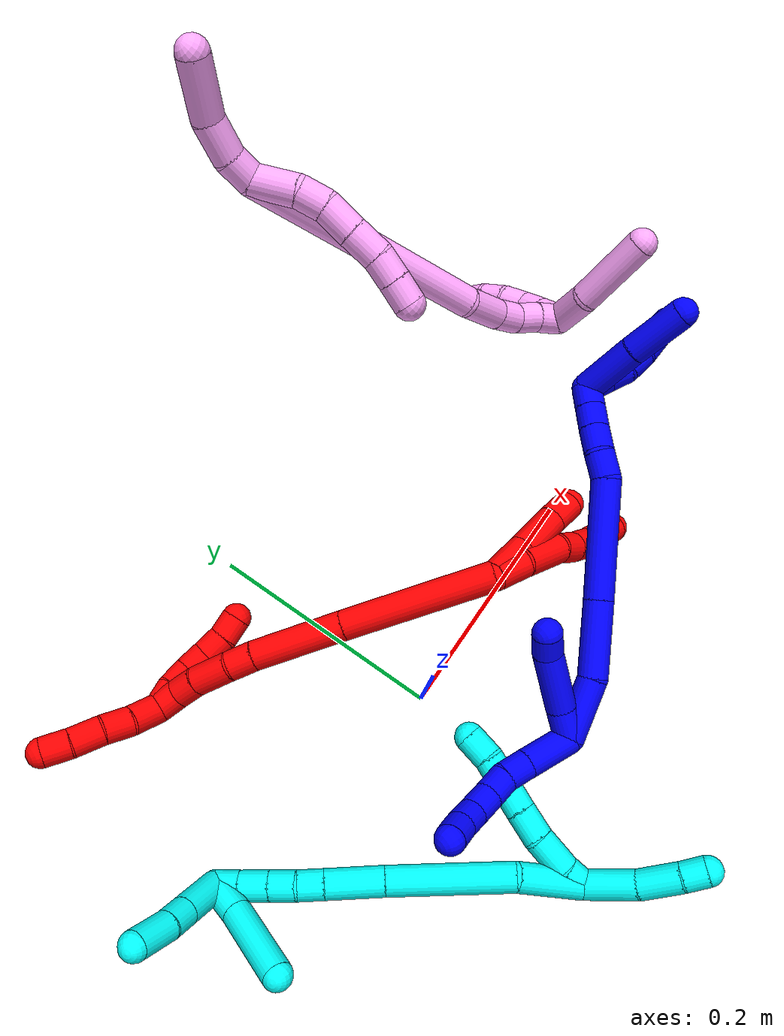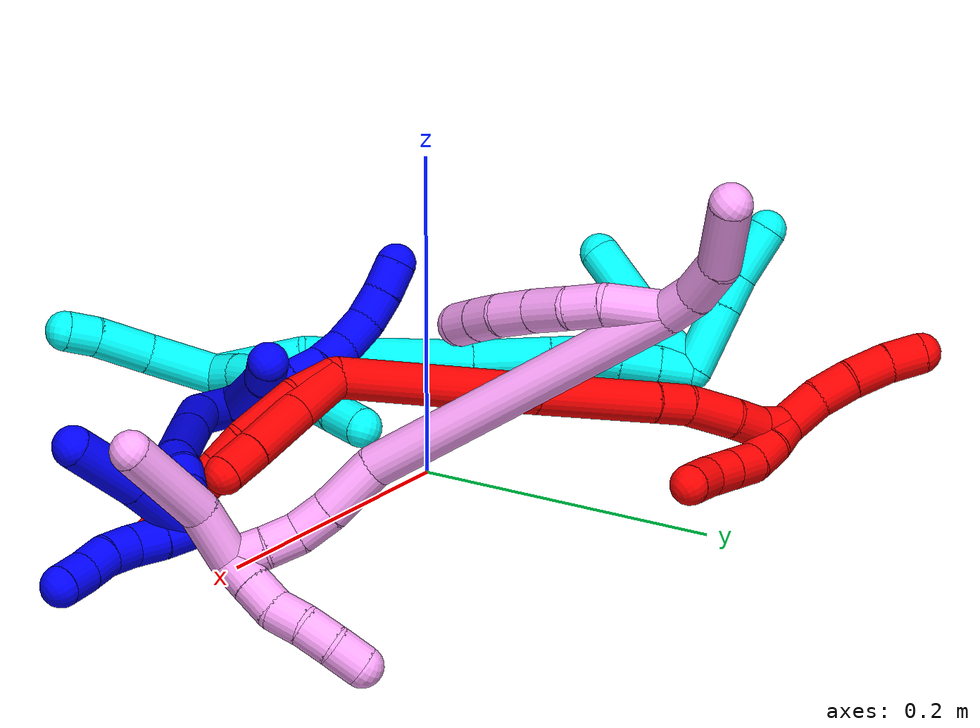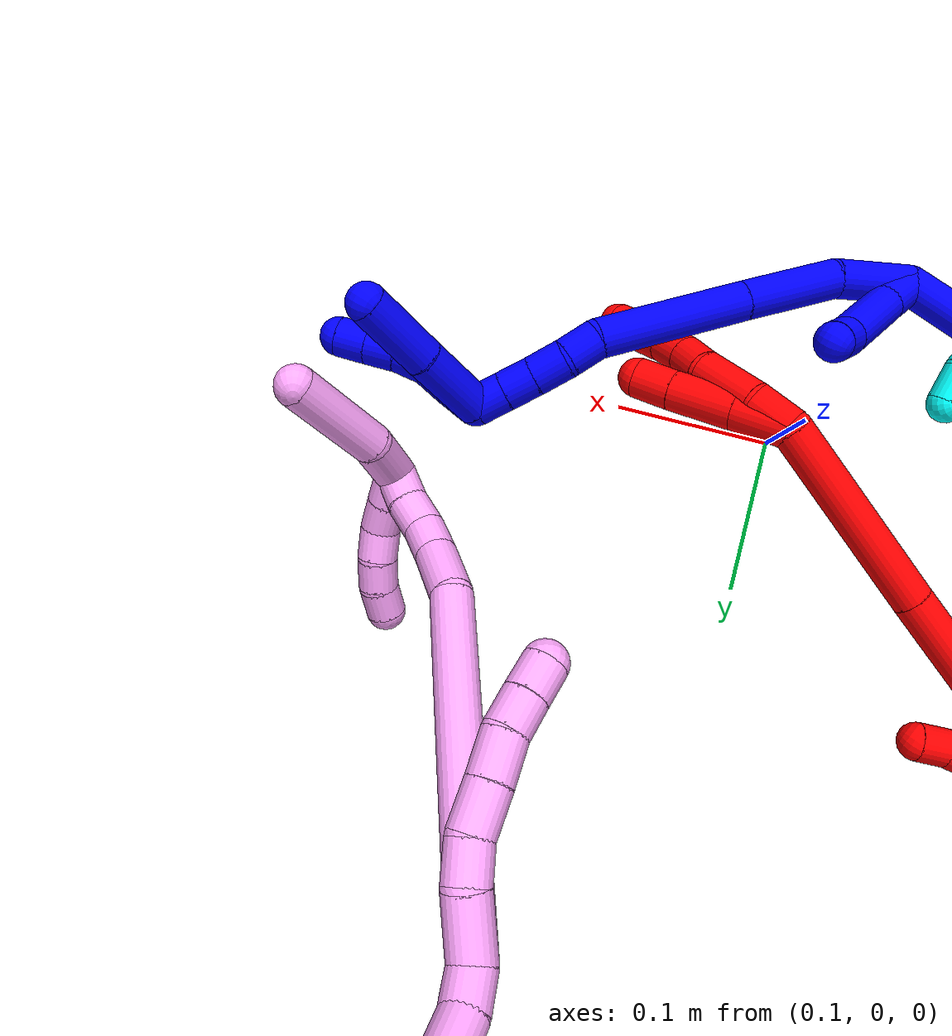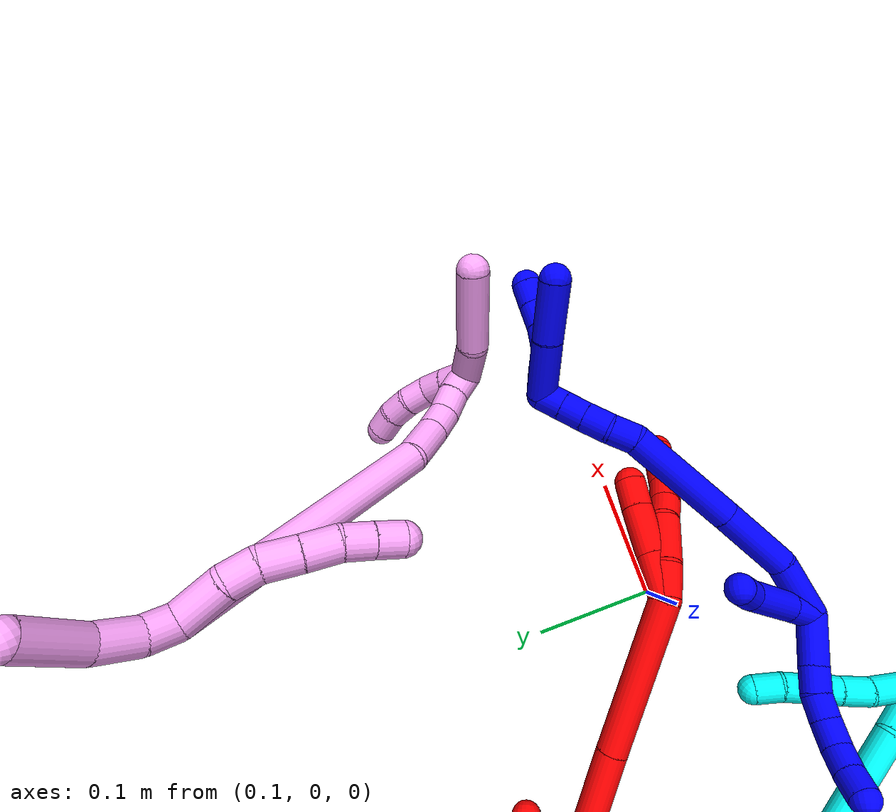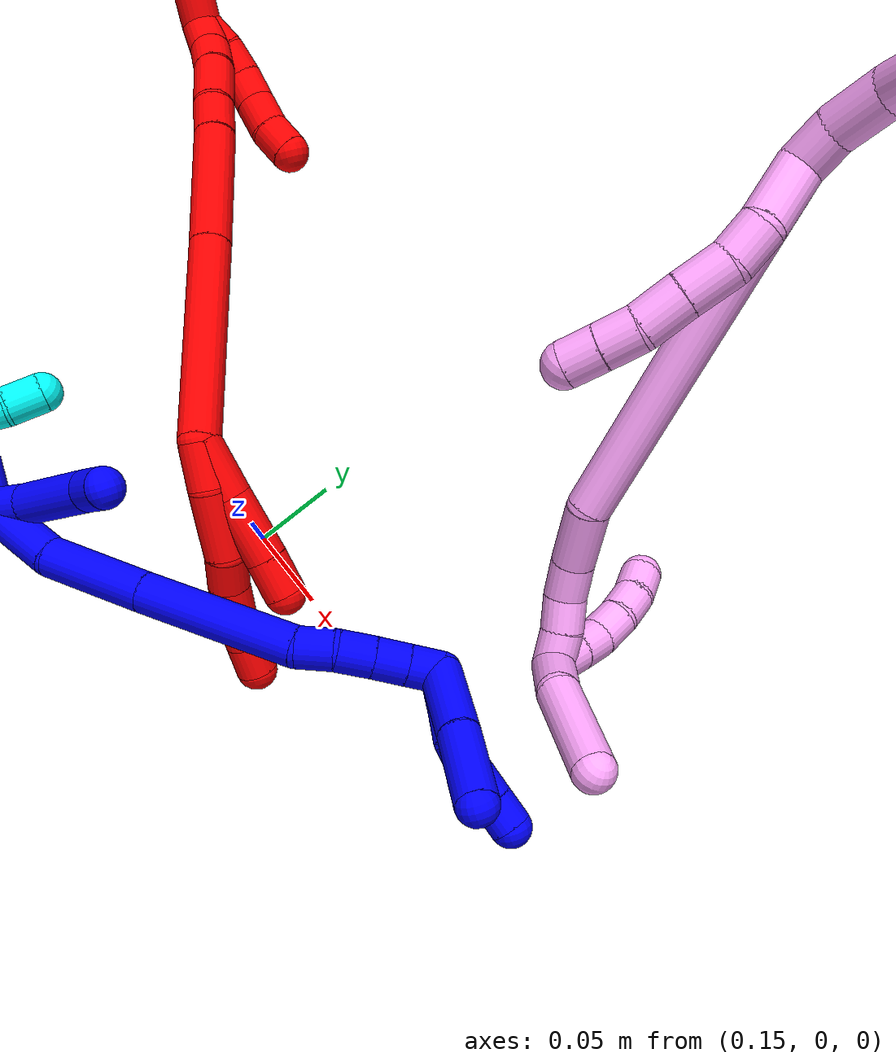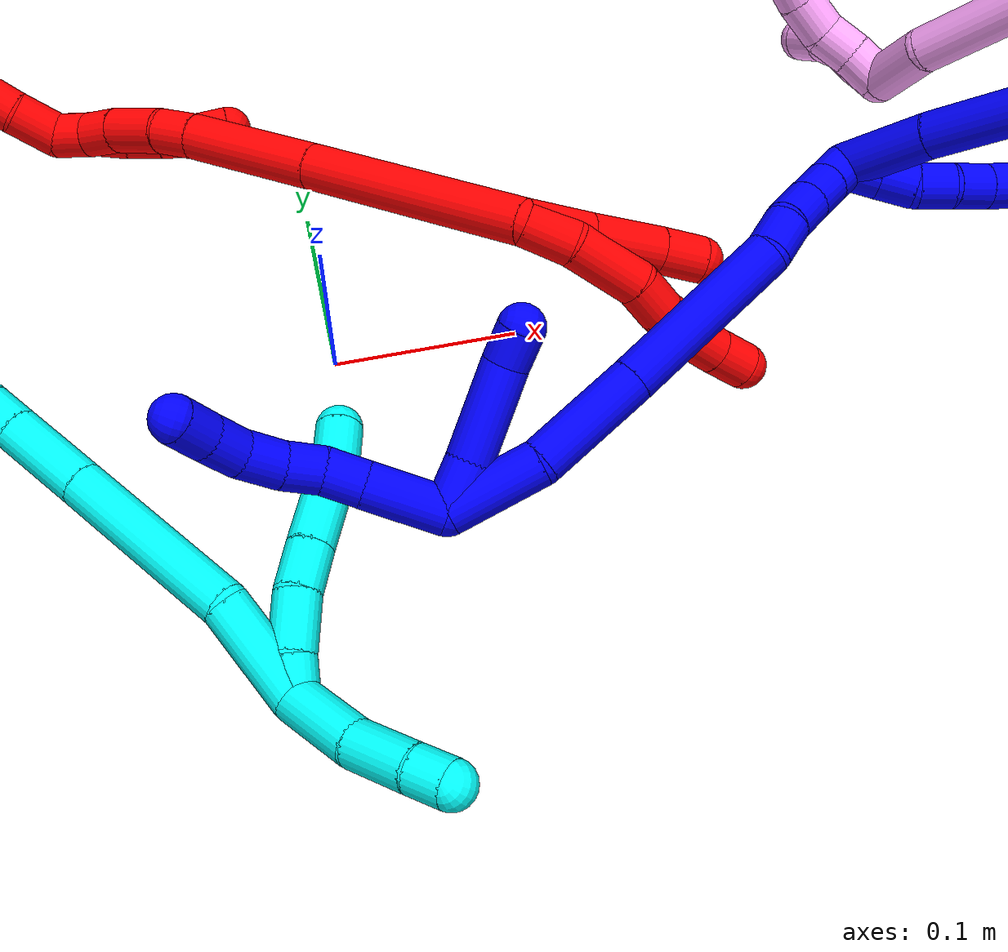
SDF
<sdf version="1.7">
 <world name="default">
  <plugin name="TubeGeneratorPlugin" filename="libtube_generator_plugin.so"/>
  <model name="photoneo_s_sensor">
   <static>1</static>
   <pose>0 0 2 1.57079 1.57079 3.14159</pose>
   <link name="link">
    <inertial><mass>0.1</mass></inertial>
    <sensor name="sensor" type="depth">
     <update_rate>30</update_rate>
     <camera>
      <horizontal_fov>1.22</horizontal_fov>
      <image><width>1920</width><height>1200</height><format>B8G8R8</format></image>
      <clip><near>0.1</near><far>4</far></clip>
      <depth_camera><output>points</output></depth_camera>
     </camera>
     <plugin name="camera_plugin" filename="libgazebo_ros_depth_camera.so">
      <baseline>0.2</baseline>
      <alwaysOn>1</alwaysOn>
      <updateRate>0.0</updateRate>
      <cameraName>camera_ir</cameraName>
      <imageTopicName>/camera/color/image_raw</imageTopicName>
      <cameraInfoTopicName>/camera/color/camera_info</cameraInfoTopicName>
      <depthImageTopicName>/camera/depth/image_raw</depthImageTopicName>
      <depthImageCameraInfoTopicName>/camera/depth/camera_info</depthImageCameraInfoTopicName>
      <pointCloudTopicName>/camera/depth/points</pointCloudTopicName>
      <frameName>fr_optical</frameName>
      <pointCloudCutoff>0.1</pointCloudCutoff>
      <pointCloudCutoffMax>2.0</pointCloudCutoffMax>
      <distortionK1>0</distortionK1>
      <distortionK2>0</distortionK2>
      <distortionK3>0</distortionK3>
      <distortionT1>0</distortionT1>
      <distortionT2>0</distortionT2>
      <CxPrime>0</CxPrime>
      <Cx>0</Cx>
      <Cy>0</Cy>
      <focalLength>0</focalLength>
      <hackBaseline>0</hackBaseline>
     </plugin>
    </sensor>
   </link>
  </model>
  <gravity>0 0 -9.8</gravity>
  <magnetic_field>6e-06 2.3e-05 -4.2e-05</magnetic_field>
  <atmosphere type="adiabatic"/>
  <physics name="default_physics" default="0" type="ode">
   <max_step_size>0.003</max_step_size>
   <real_time_factor>1</real_time_factor>
   <real_time_update_rate>1000</real_time_update_rate>
   <max_contacts>10000</max_contacts>
   <ode>
    <solver>
     <type>quick</type>
     <iters>100</iters>
     <sor>1.3</sor>
     <use_dynamic_moi_rescaling>0</use_dynamic_moi_rescaling>
    </solver>
    <constraints>
     <contact_max_correcting_vel>0</contact_max_correcting_vel>
     <contact_surface_layer>0.001</contact_surface_layer>
     <cfm>0</cfm>
     <erp>0.2</erp>
    </constraints>
   </ode>
  </physics>
  <scene><ambient>0.4 0.4 0.4 1</ambient><background>0.7 0.7 0.7 1</background><shadows>0</shadows></scene>
  <audio><device>default</device></audio>
  <spherical_coordinates>
   <surface_model>EARTH_WGS84</surface_model>
   <latitude_deg>0</latitude_deg>
   <longitude_deg>0</longitude_deg>
   <elevation>0</elevation>
   <heading_deg>0</heading_deg>
  </spherical_coordinates>
  <model name="bin">
   <static>1</static>
   <link name="bottom">
    <collision name="collision-bottom">
     <pose>0 0 -0.01 0 -0 0</pose>
     <geometry><box><size>0.8 0.6 0.02</size></box></geometry>
     <surface>
      <friction><ode><mu>100</mu><mu2>100</mu2></ode></friction>
      <contact><collide_bitmask>65535</collide_bitmask></contact>
     </surface>
    </collision>
   </link>
   <link name="west_wall">
    <collision name="collision-west_wall">
     <pose>-0.41 0 0.1 0 -0 0</pose>
     <geometry><box><size>0.02 0.6 0.2</size></box></geometry>
     <surface>
      <friction><ode><mu>100</mu><mu2>100</mu2></ode></friction>
      <contact><collide_bitmask>65535</collide_bitmask></contact>
     </surface>
    </collision>
   </link>
   <link name="east_wall">
    <collision name="collision-east_wall">
     <pose>0.41 0 0.1 0 -0 0</pose>
     <geometry><box><size>0.02 0.6 0.2</size></box></geometry>
     <surface>
      <friction><ode><mu>100</mu><mu2>100</mu2></ode></friction>
      <contact><collide_bitmask>65535</collide_bitmask></contact>
     </surface>
    </collision>
   </link>
   <link name="south_wall">
    <collision name="collision-south_wall">
     <pose>0 -0.31 0.1 0 -0 0</pose>
     <geometry><box><size>0.8 0.02 0.2</size></box></geometry>
     <surface>
      <friction><ode><mu>100</mu><mu2>100</mu2></ode></friction>
      <contact><collide_bitmask>65535</collide_bitmask></contact>
     </surface>
    </collision>
   </link>
   <link name="north_wall">
    <collision name="collision-north_wall">
     <pose>0 0.31 0.1 0 -0 0</pose>
     <geometry><box><size>0.8 0.02 0.2</size></box></geometry>
     <surface>
      <friction><ode><mu>100</mu><mu2>100</mu2></ode></friction>
      <contact><collide_bitmask>65535</collide_bitmask></contact>
     </surface>
    </collision>
   </link>
  </model>
  <model name="1">
   <static>0</static>
   <link name="1">
    <collision name="collision-cylinder-e_1_2_8">
     <pose>0.000926 -0.003352 -0.021449 2.98657 0.042642 0.535924</pose>
     <geometry><cylinder><radius>0.0125</radius><length>0.043457</length></cylinder></geometry>
     <surface>
      <friction><ode><mu>1.16</mu><mu2>1.16</mu2><slip1>0</slip1><slip2>0</slip2></ode></friction>
      <contact><ode><kp>1e+06</kp><kd>1</kd><max_vel>0</max_vel><min_depth>0.001</min_depth></ode></contact>
     </surface>
    </collision>
    <visual name="visual-cylinder-e_1_2_8">
     <pose>0.000926 -0.003352 -0.021449 2.98657 0.042642 0.535924</pose>
     <geometry><cylinder><radius>0.0125</radius><length>0.043457</length></cylinder></geometry>
     <material><ambient>0 0 1 1</ambient></material>
    </visual>
    <collision name="collision-cylinder-e_2_8_9">
     <pose>0.00227 -0.007927 -0.053699 3.02885 0.038426 0.656372</pose>
     <geometry><cylinder><radius>0.0125</radius><length>0.021757</length></cylinder></geometry>
     <surface>
      <friction><ode><mu>1.16</mu><mu2>1.16</mu2><slip1>0</slip1><slip2>0</slip2></ode></friction>
      <contact><ode><kp>1e+06</kp><kd>1</kd><max_vel>0</max_vel><min_depth>0.001</min_depth></ode></contact>
     </surface>
    </collision>
    <visual name="visual-cylinder-e_2_8_9">
     <pose>0.00227 -0.007927 -0.053699 3.02885 0.038426 0.656372</pose>
     <geometry><cylinder><radius>0.0125</radius><length>0.021757</length></cylinder></geometry>
     <material><ambient>0 0 1 1</ambient></material>
    </visual>
    <collision name="collision-cylinder-e_3_9_10">
     <pose>0.000575 -0.009102 -0.074659 -3.13692 -0.205103 3.09622</pose>
     <geometry><cylinder><radius>0.0125</radius><length>0.020754</length></cylinder></geometry>
     <surface>
      <friction><ode><mu>1.16</mu><mu2>1.16</mu2><slip1>0</slip1><slip2>0</slip2></ode></friction>
      <contact><ode><kp>1e+06</kp><kd>1</kd><max_vel>0</max_vel><min_depth>0.001</min_depth></ode></contact>
     </surface>
    </collision>
    <visual name="visual-cylinder-e_3_9_10">
     <pose>0.000575 -0.009102 -0.074659 -3.13692 -0.205103 3.09622</pose>
     <geometry><cylinder><radius>0.0125</radius><length>0.020754</length></cylinder></geometry>
     <material><ambient>0 0 1 1</ambient></material>
    </visual>
    <collision name="collision-cylinder-e_4_10_11">
     <pose>-0.002664 -0.006641 -0.095869 -2.92656 -0.099172 0.861921</pose>
     <geometry><cylinder><radius>0.0125</radius><length>0.022733</length></cylinder></geometry>
     <surface>
      <friction><ode><mu>1.16</mu><mu2>1.16</mu2><slip1>0</slip1><slip2>0</slip2></ode></friction>
      <contact><ode><kp>1e+06</kp><kd>1</kd><max_vel>0</max_vel><min_depth>0.001</min_depth></ode></contact>
     </surface>
    </collision>
    <visual name="visual-cylinder-e_4_10_11">
     <pose>-0.002664 -0.006641 -0.095869 -2.92656 -0.099172 0.861921</pose>
     <geometry><cylinder><radius>0.0125</radius><length>0.022733</length></cylinder></geometry>
     <material><ambient>0 0 1 1</ambient></material>
    </visual>
    <collision name="collision-cylinder-e_5_11_12">
     <pose>-0.003726 0.000341 -0.116153 -2.68209 0.006189 -0.026459</pose>
     <geometry><cylinder><radius>0.0125</radius><length>0.020605</length></cylinder></geometry>
     <surface>
      <friction><ode><mu>1.16</mu><mu2>1.16</mu2><slip1>0</slip1><slip2>0</slip2></ode></friction>
      <contact><ode><kp>1e+06</kp><kd>1</kd><max_vel>0</max_vel><min_depth>0.001</min_depth></ode></contact>
     </surface>
    </collision>
    <visual name="visual-cylinder-e_5_11_12">
     <pose>-0.003726 0.000341 -0.116153 -2.68209 0.006189 -0.026459</pose>
     <geometry><cylinder><radius>0.0125</radius><length>0.020605</length></cylinder></geometry>
     <material><ambient>0 0 1 1</ambient></material>
    </visual>
    <collision name="collision-cylinder-e_6_12_6">
     <pose>-0.003768 0.010589 -0.134035 -2.56065 -0.010216 0.034172</pose>
     <geometry><cylinder><radius>0.0125</radius><length>0.020693</length></cylinder></geometry>
     <surface>
      <friction><ode><mu>1.16</mu><mu2>1.16</mu2><slip1>0</slip1><slip2>0</slip2></ode></friction>
      <contact><ode><kp>1e+06</kp><kd>1</kd><max_vel>0</max_vel><min_depth>0.001</min_depth></ode></contact>
     </surface>
    </collision>
    <visual name="visual-cylinder-e_6_12_6">
     <pose>-0.003768 0.010589 -0.134035 -2.56065 -0.010216 0.034172</pose>
     <geometry><cylinder><radius>0.0125</radius><length>0.020693</length></cylinder></geometry>
     <material><ambient>0 0 1 1</ambient></material>
    </visual>
    <collision name="collision-cylinder-e_1_2_13">
     <pose>0.013108 0.003831 0.001223 -1.26171 1.27311 -0.990161</pose>
     <geometry><cylinder><radius>0.0125</radius><length>0.027422</length></cylinder></geometry>
     <surface>
      <friction><ode><mu>1.16</mu><mu2>1.16</mu2><slip1>0</slip1><slip2>0</slip2></ode></friction>
      <contact><ode><kp>1e+06</kp><kd>1</kd><max_vel>0</max_vel><min_depth>0.001</min_depth></ode></contact>
     </surface>
    </collision>
    <visual name="visual-cylinder-e_1_2_13">
     <pose>0.013108 0.003831 0.001223 -1.26171 1.27311 -0.990161</pose>
     <geometry><cylinder><radius>0.0125</radius><length>0.027422</length></cylinder></geometry>
     <material><ambient>0 0 1 1</ambient></material>
    </visual>
    <collision name="collision-cylinder-e_2_13_14">
     <pose>0.049959 0.018603 0.002453 -1.57021 1.13899 -1.13846</pose>
     <geometry><cylinder><radius>0.0125</radius><length>0.052285</length></cylinder></geometry>
     <surface>
      <friction><ode><mu>1.16</mu><mu2>1.16</mu2><slip1>0</slip1><slip2>0</slip2></ode></friction>
      <contact><ode><kp>1e+06</kp><kd>1</kd><max_vel>0</max_vel><min_depth>0.001</min_depth></ode></contact>
     </surface>
    </collision>
    <visual name="visual-cylinder-e_2_13_14">
     <pose>0.049959 0.018603 0.002453 -1.57021 1.13899 -1.13846</pose>
     <geometry><cylinder><radius>0.0125</radius><length>0.052285</length></cylinder></geometry>
     <material><ambient>0 0 1 1</ambient></material>
    </visual>
    <collision name="collision-cylinder-e_3_14_5">
     <pose>0.081417 0.036133 0.002381 -1.58268 0.863915 -0.87299</pose>
     <geometry><cylinder><radius>0.0125</radius><length>0.020293</length></cylinder></geometry>
     <surface>
      <friction><ode><mu>1.16</mu><mu2>1.16</mu2><slip1>0</slip1><slip2>0</slip2></ode></friction>
      <contact><ode><kp>1e+06</kp><kd>1</kd><max_vel>0</max_vel><min_depth>0.001</min_depth></ode></contact>
     </surface>
    </collision>
    <visual name="visual-cylinder-e_3_14_5">
     <pose>0.081417 0.036133 0.002381 -1.58268 0.863915 -0.87299</pose>
     <geometry><cylinder><radius>0.0125</radius><length>0.020293</length></cylinder></geometry>
     <material><ambient>0 0 1 1</ambient></material>
    </visual>
    <collision name="collision-cylinder-e_1_2_15">
     <pose>0.016955 0.00983 0.017413 -0.513935 0.703279 -0.192225</pose>
     <geometry><cylinder><radius>0.0125</radius><length>0.052433</length></cylinder></geometry>
     <surface>
      <friction><ode><mu>1.16</mu><mu2>1.16</mu2><slip1>0</slip1><slip2>0</slip2></ode></friction>
      <contact><ode><kp>1e+06</kp><kd>1</kd><max_vel>0</max_vel><min_depth>0.001</min_depth></ode></contact>
     </surface>
    </collision>
    <visual name="visual-cylinder-e_1_2_15">
     <pose>0.016955 0.00983 0.017413 -0.513935 0.703279 -0.192225</pose>
     <geometry><cylinder><radius>0.0125</radius><length>0.052433</length></cylinder></geometry>
     <material><ambient>0 0 1 1</ambient></material>
    </visual>
    <collision name="collision-cylinder-e_2_15_16">
     <pose>0.060426 0.026247 0.051254 -0.381293 0.982231 -0.205703</pose>
     <geometry><cylinder><radius>0.0125</radius><length>0.063761</length></cylinder></geometry>
     <surface>
      <friction><ode><mu>1.16</mu><mu2>1.16</mu2><slip1>0</slip1><slip2>0</slip2></ode></friction>
      <contact><ode><kp>1e+06</kp><kd>1</kd><max_vel>0</max_vel><min_depth>0.001</min_depth></ode></contact>
     </surface>
    </collision>
    <visual name="visual-cylinder-e_2_15_16">
     <pose>0.060426 0.026247 0.051254 -0.381293 0.982231 -0.205703</pose>
     <geometry><cylinder><radius>0.0125</radius><length>0.063761</length></cylinder></geometry>
     <material><ambient>0 0 1 1</ambient></material>
    </visual>
    <collision name="collision-cylinder-e_3_16_17">
     <pose>0.128698 0.043588 0.092204 -0.413341 1.00058 -0.228241</pose>
     <geometry><cylinder><radius>0.0125</radius><length>0.099208</length></cylinder></geometry>
     <surface>
      <friction><ode><mu>1.16</mu><mu2>1.16</mu2><slip1>0</slip1><slip2>0</slip2></ode></friction>
      <contact><ode><kp>1e+06</kp><kd>1</kd><max_vel>0</max_vel><min_depth>0.001</min_depth></ode></contact>
     </surface>
    </collision>
    <visual name="visual-cylinder-e_3_16_17">
     <pose>0.128698 0.043588 0.092204 -0.413341 1.00058 -0.228241</pose>
     <geometry><cylinder><radius>0.0125</radius><length>0.099208</length></cylinder></geometry>
     <material><ambient>0 0 1 1</ambient></material>
    </visual>
    <collision name="collision-cylinder-e_4_17_18">
     <pose>0.180988 0.053869 0.120475 0.12594 1.22639 0.088682</pose>
     <geometry><cylinder><radius>0.0125</radius><length>0.022383</length></cylinder></geometry>
     <surface>
      <friction><ode><mu>1.16</mu><mu2>1.16</mu2><slip1>0</slip1><slip2>0</slip2></ode></friction>
      <contact><ode><kp>1e+06</kp><kd>1</kd><max_vel>0</max_vel><min_depth>0.001</min_depth></ode></contact>
     </surface>
    </collision>
    <visual name="visual-cylinder-e_4_17_18">
     <pose>0.180988 0.053869 0.120475 0.12594 1.22639 0.088682</pose>
     <geometry><cylinder><radius>0.0125</radius><length>0.022383</length></cylinder></geometry>
     <material><ambient>0 0 1 1</ambient></material>
    </visual>
    <collision name="collision-cylinder-e_5_18_19">
     <pose>0.200833 0.051042 0.12965 0.409064 1.0049 0.226983</pose>
     <geometry><cylinder><radius>0.0125</radius><length>0.02206</length></cylinder></geometry>
     <surface>
      <friction><ode><mu>1.16</mu><mu2>1.16</mu2><slip1>0</slip1><slip2>0</slip2></ode></friction>
      <contact><ode><kp>1e+06</kp><kd>1</kd><max_vel>0</max_vel><min_depth>0.001</min_depth></ode></contact>
     </surface>
    </collision>
    <visual name="visual-cylinder-e_5_18_19">
     <pose>0.200833 0.051042 0.12965 0.409064 1.0049 0.226983</pose>
     <geometry><cylinder><radius>0.0125</radius><length>0.02206</length></cylinder></geometry>
     <material><ambient>0 0 1 1</ambient></material>
    </visual>
    <collision name="collision-cylinder-e_6_19_20">
     <pose>0.218621 0.046858 0.140203 0.34314 0.999828 0.188719</pose>
     <geometry><cylinder><radius>0.0125</radius><length>0.020149</length></cylinder></geometry>
     <surface>
      <friction><ode><mu>1.16</mu><mu2>1.16</mu2><slip1>0</slip1><slip2>0</slip2></ode></friction>
      <contact><ode><kp>1e+06</kp><kd>1</kd><max_vel>0</max_vel><min_depth>0.001</min_depth></ode></contact>
     </surface>
    </collision>
    <visual name="visual-cylinder-e_6_19_20">
     <pose>0.218621 0.046858 0.140203 0.34314 0.999828 0.188719</pose>
     <geometry><cylinder><radius>0.0125</radius><length>0.020149</length></cylinder></geometry>
     <material><ambient>0 0 1 1</ambient></material>
    </visual>
    <collision name="collision-cylinder-e_7_20_1">
     <pose>0.235526 0.043204 0.150398 0.345256 1.00225 0.190443</pose>
     <geometry><cylinder><radius>0.0125</radius><length>0.020005</length></cylinder></geometry>
     <surface>
      <friction><ode><mu>1.16</mu><mu2>1.16</mu2><slip1>0</slip1><slip2>0</slip2></ode></friction>
      <contact><ode><kp>1e+06</kp><kd>1</kd><max_vel>0</max_vel><min_depth>0.001</min_depth></ode></contact>
     </surface>
    </collision>
    <visual name="visual-cylinder-e_7_20_1">
     <pose>0.235526 0.043204 0.150398 0.345256 1.00225 0.190443</pose>
     <geometry><cylinder><radius>0.0125</radius><length>0.020005</length></cylinder></geometry>
     <material><ambient>0 0 1 1</ambient></material>
    </visual>
    <collision name="collision-cylinder-e_1_1_21">
     <pose>0.243693 0.04368 0.165194 -0.232046 -0.026199 0.003054</pose>
     <geometry><cylinder><radius>0.0125</radius><length>0.02</length></cylinder></geometry>
     <surface>
      <friction><ode><mu>1.16</mu><mu2>1.16</mu2><slip1>0</slip1><slip2>0</slip2></ode></friction>
      <contact><ode><kp>1e+06</kp><kd>1</kd><max_vel>0</max_vel><min_depth>0.001</min_depth></ode></contact>
     </surface>
    </collision>
    <visual name="visual-cylinder-e_1_1_21">
     <pose>0.243693 0.04368 0.165194 -0.232046 -0.026199 0.003054</pose>
     <geometry><cylinder><radius>0.0125</radius><length>0.02</length></cylinder></geometry>
     <material><ambient>0 0 1 1</ambient></material>
    </visual>
    <collision name="collision-cylinder-e_2_21_22">
     <pose>0.242907 0.049104 0.184408 -0.318243 -0.052408 0.008412</pose>
     <geometry><cylinder><radius>0.0125</radius><length>0.02</length></cylinder></geometry>
     <surface>
      <friction><ode><mu>1.16</mu><mu2>1.16</mu2><slip1>0</slip1><slip2>0</slip2></ode></friction>
      <contact><ode><kp>1e+06</kp><kd>1</kd><max_vel>0</max_vel><min_depth>0.001</min_depth></ode></contact>
     </surface>
    </collision>
    <visual name="visual-cylinder-e_2_21_22">
     <pose>0.242907 0.049104 0.184408 -0.318243 -0.052408 0.008412</pose>
     <geometry><cylinder><radius>0.0125</radius><length>0.02</length></cylinder></geometry>
     <material><ambient>0 0 1 1</ambient></material>
    </visual>
    <collision name="collision-cylinder-e_3_22_23">
     <pose>0.244918 0.055084 0.203135 -0.299681 0.256299 -0.038902</pose>
     <geometry><cylinder><radius>0.0125</radius><length>0.02</length></cylinder></geometry>
     <surface>
      <friction><ode><mu>1.16</mu><mu2>1.16</mu2><slip1>0</slip1><slip2>0</slip2></ode></friction>
      <contact><ode><kp>1e+06</kp><kd>1</kd><max_vel>0</max_vel><min_depth>0.001</min_depth></ode></contact>
     </surface>
    </collision>
    <visual name="visual-cylinder-e_3_22_23">
     <pose>0.244918 0.055084 0.203135 -0.299681 0.256299 -0.038902</pose>
     <geometry><cylinder><radius>0.0125</radius><length>0.02</length></cylinder></geometry>
     <material><ambient>0 0 1 1</ambient></material>
    </visual>
    <collision name="collision-cylinder-e_4_23_24">
     <pose>0.250787 0.05871 0.221773 -0.081826 0.339873 -0.014048</pose>
     <geometry><cylinder><radius>0.0125</radius><length>0.02</length></cylinder></geometry>
     <surface>
      <friction><ode><mu>1.16</mu><mu2>1.16</mu2><slip1>0</slip1><slip2>0</slip2></ode></friction>
      <contact><ode><kp>1e+06</kp><kd>1</kd><max_vel>0</max_vel><min_depth>0.001</min_depth></ode></contact>
     </surface>
    </collision>
    <visual name="visual-cylinder-e_4_23_24">
     <pose>0.250787 0.05871 0.221773 -0.081826 0.339873 -0.014048</pose>
     <geometry><cylinder><radius>0.0125</radius><length>0.02</length></cylinder></geometry>
     <material><ambient>0 0 1 1</ambient></material>
    </visual>
    <collision name="collision-cylinder-e_5_24_4">
     <pose>0.257691 0.061099 0.24037 -0.174097 0.365053 -0.032214</pose>
     <geometry><cylinder><radius>0.0125</radius><length>0.02</length></cylinder></geometry>
     <surface>
      <friction><ode><mu>1.16</mu><mu2>1.16</mu2><slip1>0</slip1><slip2>0</slip2></ode></friction>
      <contact><ode><kp>1e+06</kp><kd>1</kd><max_vel>0</max_vel><min_depth>0.001</min_depth></ode></contact>
     </surface>
    </collision>
    <visual name="visual-cylinder-e_5_24_4">
     <pose>0.257691 0.061099 0.24037 -0.174097 0.365053 -0.032214</pose>
     <geometry><cylinder><radius>0.0125</radius><length>0.02</length></cylinder></geometry>
     <material><ambient>0 0 1 1</ambient></material>
    </visual>
    <collision name="collision-cylinder-e_1_1_25">
     <pose>0.248038 0.063605 0.167098 -1.08858 0.16138 -0.097814</pose>
     <geometry><cylinder><radius>0.0125</radius><length>0.050828</length></cylinder></geometry>
     <surface>
      <friction><ode><mu>1.16</mu><mu2>1.16</mu2><slip1>0</slip1><slip2>0</slip2></ode></friction>
      <contact><ode><kp>1e+06</kp><kd>1</kd><max_vel>0</max_vel><min_depth>0.001</min_depth></ode></contact>
     </surface>
    </collision>
    <visual name="visual-cylinder-e_1_1_25">
     <pose>0.248038 0.063605 0.167098 -1.08858 0.16138 -0.097814</pose>
     <geometry><cylinder><radius>0.0125</radius><length>0.050828</length></cylinder></geometry>
     <material><ambient>0 0 1 1</ambient></material>
    </visual>
    <collision name="collision-cylinder-e_2_25_3">
     <pose>0.255262 0.106642 0.191434 -1.02284 0.128086 -0.071952</pose>
     <geometry><cylinder><radius>0.0125</radius><length>0.049172</length></cylinder></geometry>
     <surface>
      <friction><ode><mu>1.16</mu><mu2>1.16</mu2><slip1>0</slip1><slip2>0</slip2></ode></friction>
      <contact><ode><kp>1e+06</kp><kd>1</kd><max_vel>0</max_vel><min_depth>0.001</min_depth></ode></contact>
     </surface>
    </collision>
    <visual name="visual-cylinder-e_2_25_3">
     <pose>0.255262 0.106642 0.191434 -1.02284 0.128086 -0.071952</pose>
     <geometry><cylinder><radius>0.0125</radius><length>0.049172</length></cylinder></geometry>
     <material><ambient>0 0 1 1</ambient></material>
    </visual>
    <collision name="collision-sphere-3">
     <pose>0.258403 0.127457 0.204137 0 -0 0</pose>
     <geometry><sphere><radius>0.0125</radius></sphere></geometry>
     <surface>
      <friction><ode><mu>1.16</mu><mu2>1.16</mu2><slip1>0</slip1><slip2>0</slip2></ode></friction>
      <contact><ode><kp>1e+06</kp><kd>1</kd><max_vel>0</max_vel><min_depth>0.001</min_depth></ode></contact>
     </surface>
    </collision>
    <visual name="visual-sphere-3">
     <pose>0.258403 0.127457 0.204137 0 -0 0</pose>
     <geometry><sphere><radius>0.0125</radius></sphere></geometry>
     <material><ambient>0 0 1 1</ambient></material>
    </visual>
    <collision name="collision-sphere-25">
     <pose>0.252122 0.085828 0.178731 0 -0 0</pose>
     <geometry><sphere><radius>0.0125</radius></sphere></geometry>
     <surface>
      <friction><ode><mu>1.16</mu><mu2>1.16</mu2><slip1>0</slip1><slip2>0</slip2></ode></friction>
      <contact><ode><kp>1e+06</kp><kd>1</kd><max_vel>0</max_vel><min_depth>0.001</min_depth></ode></contact>
     </surface>
    </collision>
    <visual name="visual-sphere-25">
     <pose>0.252122 0.085828 0.178731 0 -0 0</pose>
     <geometry><sphere><radius>0.0125</radius></sphere></geometry>
     <material><ambient>0 0 1 1</ambient></material>
    </visual>
    <collision name="collision-sphere-4">
     <pose>0.261261 0.062717 0.24957 0 -0 0</pose>
     <geometry><sphere><radius>0.0125</radius></sphere></geometry>
     <surface>
      <friction><ode><mu>1.16</mu><mu2>1.16</mu2><slip1>0</slip1><slip2>0</slip2></ode></friction>
      <contact><ode><kp>1e+06</kp><kd>1</kd><max_vel>0</max_vel><min_depth>0.001</min_depth></ode></contact>
     </surface>
    </collision>
    <visual name="visual-sphere-4">
     <pose>0.261261 0.062717 0.24957 0 -0 0</pose>
     <geometry><sphere><radius>0.0125</radius></sphere></geometry>
     <material><ambient>0 0 1 1</ambient></material>
    </visual>
    <collision name="collision-sphere-24">
     <pose>0.254121 0.059481 0.23117 0 -0 0</pose>
     <geometry><sphere><radius>0.0125</radius></sphere></geometry>
     <surface>
      <friction><ode><mu>1.16</mu><mu2>1.16</mu2><slip1>0</slip1><slip2>0</slip2></ode></friction>
      <contact><ode><kp>1e+06</kp><kd>1</kd><max_vel>0</max_vel><min_depth>0.001</min_depth></ode></contact>
     </surface>
    </collision>
    <visual name="visual-sphere-24">
     <pose>0.254121 0.059481 0.23117 0 -0 0</pose>
     <geometry><sphere><radius>0.0125</radius></sphere></geometry>
     <material><ambient>0 0 1 1</ambient></material>
    </visual>
    <collision name="collision-sphere-23">
     <pose>0.247453 0.05794 0.212377 0 -0 0</pose>
     <geometry><sphere><radius>0.0125</radius></sphere></geometry>
     <surface>
      <friction><ode><mu>1.16</mu><mu2>1.16</mu2><slip1>0</slip1><slip2>0</slip2></ode></friction>
      <contact><ode><kp>1e+06</kp><kd>1</kd><max_vel>0</max_vel><min_depth>0.001</min_depth></ode></contact>
     </surface>
    </collision>
    <visual name="visual-sphere-23">
     <pose>0.247453 0.05794 0.212377 0 -0 0</pose>
     <geometry><sphere><radius>0.0125</radius></sphere></geometry>
     <material><ambient>0 0 1 1</ambient></material>
    </visual>
    <collision name="collision-sphere-22">
     <pose>0.242383 0.052228 0.193893 0 -0 0</pose>
     <geometry><sphere><radius>0.0125</radius></sphere></geometry>
     <surface>
      <friction><ode><mu>1.16</mu><mu2>1.16</mu2><slip1>0</slip1><slip2>0</slip2></ode></friction>
      <contact><ode><kp>1e+06</kp><kd>1</kd><max_vel>0</max_vel><min_depth>0.001</min_depth></ode></contact>
     </surface>
    </collision>
    <visual name="visual-sphere-22">
     <pose>0.242383 0.052228 0.193893 0 -0 0</pose>
     <geometry><sphere><radius>0.0125</radius></sphere></geometry>
     <material><ambient>0 0 1 1</ambient></material>
    </visual>
    <collision name="collision-sphere-21">
     <pose>0.243431 0.045979 0.174923 0 -0 0</pose>
     <geometry><sphere><radius>0.0125</radius></sphere></geometry>
     <surface>
      <friction><ode><mu>1.16</mu><mu2>1.16</mu2><slip1>0</slip1><slip2>0</slip2></ode></friction>
      <contact><ode><kp>1e+06</kp><kd>1</kd><max_vel>0</max_vel><min_depth>0.001</min_depth></ode></contact>
     </surface>
    </collision>
    <visual name="visual-sphere-21">
     <pose>0.243431 0.045979 0.174923 0 -0 0</pose>
     <geometry><sphere><radius>0.0125</radius></sphere></geometry>
     <material><ambient>0 0 1 1</ambient></material>
    </visual>
    <collision name="collision-sphere-1">
     <pose>0.243955 0.041381 0.155466 0 -0 0</pose>
     <geometry><sphere><radius>0.0125</radius></sphere></geometry>
     <surface>
      <friction><ode><mu>1.16</mu><mu2>1.16</mu2><slip1>0</slip1><slip2>0</slip2></ode></friction>
      <contact><ode><kp>1e+06</kp><kd>1</kd><max_vel>0</max_vel><min_depth>0.001</min_depth></ode></contact>
     </surface>
    </collision>
    <visual name="visual-sphere-1">
     <pose>0.243955 0.041381 0.155466 0 -0 0</pose>
     <geometry><sphere><radius>0.0125</radius></sphere></geometry>
     <material><ambient>0 0 1 1</ambient></material>
    </visual>
    <collision name="collision-sphere-12">
     <pose>-0.003662 0.004911 -0.125387 0 -0 0</pose>
     <geometry><sphere><radius>0.0125</radius></sphere></geometry>
     <surface>
      <friction><ode><mu>1.16</mu><mu2>1.16</mu2><slip1>0</slip1><slip2>0</slip2></ode></friction>
      <contact><ode><kp>1e+06</kp><kd>1</kd><max_vel>0</max_vel><min_depth>0.001</min_depth></ode></contact>
     </surface>
    </collision>
    <visual name="visual-sphere-12">
     <pose>-0.003662 0.004911 -0.125387 0 -0 0</pose>
     <geometry><sphere><radius>0.0125</radius></sphere></geometry>
     <material><ambient>0 0 1 1</ambient></material>
    </visual>
    <collision name="collision-sphere-11">
     <pose>-0.003789 -0.004228 -0.106919 0 -0 0</pose>
     <geometry><sphere><radius>0.0125</radius></sphere></geometry>
     <surface>
      <friction><ode><mu>1.16</mu><mu2>1.16</mu2><slip1>0</slip1><slip2>0</slip2></ode></friction>
      <contact><ode><kp>1e+06</kp><kd>1</kd><max_vel>0</max_vel><min_depth>0.001</min_depth></ode></contact>
     </surface>
    </collision>
    <visual name="visual-sphere-11">
     <pose>-0.003789 -0.004228 -0.106919 0 -0 0</pose>
     <geometry><sphere><radius>0.0125</radius></sphere></geometry>
     <material><ambient>0 0 1 1</ambient></material>
    </visual>
    <collision name="collision-sphere-10">
     <pose>-0.001539 -0.009055 -0.084819 0 -0 0</pose>
     <geometry><sphere><radius>0.0125</radius></sphere></geometry>
     <surface>
      <friction><ode><mu>1.16</mu><mu2>1.16</mu2><slip1>0</slip1><slip2>0</slip2></ode></friction>
      <contact><ode><kp>1e+06</kp><kd>1</kd><max_vel>0</max_vel><min_depth>0.001</min_depth></ode></contact>
     </surface>
    </collision>
    <visual name="visual-sphere-10">
     <pose>-0.001539 -0.009055 -0.084819 0 -0 0</pose>
     <geometry><sphere><radius>0.0125</radius></sphere></geometry>
     <material><ambient>0 0 1 1</ambient></material>
    </visual>
    <collision name="collision-sphere-9">
     <pose>0.002688 -0.00915 -0.0645 0 -0 0</pose>
     <geometry><sphere><radius>0.0125</radius></sphere></geometry>
     <surface>
      <friction><ode><mu>1.16</mu><mu2>1.16</mu2><slip1>0</slip1><slip2>0</slip2></ode></friction>
      <contact><ode><kp>1e+06</kp><kd>1</kd><max_vel>0</max_vel><min_depth>0.001</min_depth></ode></contact>
     </surface>
    </collision>
    <visual name="visual-sphere-9">
     <pose>0.002688 -0.00915 -0.0645 0 -0 0</pose>
     <geometry><sphere><radius>0.0125</radius></sphere></geometry>
     <material><ambient>0 0 1 1</ambient></material>
    </visual>
    <collision name="collision-sphere-2">
     <geometry><sphere><radius>0.0125</radius></sphere></geometry>
     <surface>
      <friction><ode><mu>1.16</mu><mu2>1.16</mu2><slip1>0</slip1><slip2>0</slip2></ode></friction>
      <contact><ode><kp>1e+06</kp><kd>1</kd><max_vel>0</max_vel><min_depth>0.001</min_depth></ode></contact>
     </surface>
    </collision>
    <visual name="visual-sphere-2">
     <geometry><sphere><radius>0.0125</radius></sphere></geometry>
     <material><ambient>0 0 1 1</ambient></material>
    </visual>
    <collision name="collision-sphere-19">
     <pose>0.210144 0.04869 0.135076 0 -0 0</pose>
     <geometry><sphere><radius>0.0125</radius></sphere></geometry>
     <surface>
      <friction><ode><mu>1.16</mu><mu2>1.16</mu2><slip1>0</slip1><slip2>0</slip2></ode></friction>
      <contact><ode><kp>1e+06</kp><kd>1</kd><max_vel>0</max_vel><min_depth>0.001</min_depth></ode></contact>
     </surface>
    </collision>
    <visual name="visual-sphere-19">
     <pose>0.210144 0.04869 0.135076 0 -0 0</pose>
     <geometry><sphere><radius>0.0125</radius></sphere></geometry>
     <material><ambient>0 0 1 1</ambient></material>
    </visual>
    <collision name="collision-sphere-8">
     <pose>0.001853 -0.006704 -0.042897 0 -0 0</pose>
     <geometry><sphere><radius>0.0125</radius></sphere></geometry>
     <surface>
      <friction><ode><mu>1.16</mu><mu2>1.16</mu2><slip1>0</slip1><slip2>0</slip2></ode></friction>
      <contact><ode><kp>1e+06</kp><kd>1</kd><max_vel>0</max_vel><min_depth>0.001</min_depth></ode></contact>
     </surface>
    </collision>
    <visual name="visual-sphere-8">
     <pose>0.001853 -0.006704 -0.042897 0 -0 0</pose>
     <geometry><sphere><radius>0.0125</radius></sphere></geometry>
     <material><ambient>0 0 1 1</ambient></material>
    </visual>
    <collision name="collision-sphere-6">
     <pose>-0.003873 0.016267 -0.142684 0 -0 0</pose>
     <geometry><sphere><radius>0.0125</radius></sphere></geometry>
     <surface>
      <friction><ode><mu>1.16</mu><mu2>1.16</mu2><slip1>0</slip1><slip2>0</slip2></ode></friction>
      <contact><ode><kp>1e+06</kp><kd>1</kd><max_vel>0</max_vel><min_depth>0.001</min_depth></ode></contact>
     </surface>
    </collision>
    <visual name="visual-sphere-6">
     <pose>-0.003873 0.016267 -0.142684 0 -0 0</pose>
     <geometry><sphere><radius>0.0125</radius></sphere></geometry>
     <material><ambient>0 0 1 1</ambient></material>
    </visual>
    <collision name="collision-sphere-13">
     <pose>0.026216 0.007662 0.002447 0 -0 0</pose>
     <geometry><sphere><radius>0.0125</radius></sphere></geometry>
     <surface>
      <friction><ode><mu>1.16</mu><mu2>1.16</mu2><slip1>0</slip1><slip2>0</slip2></ode></friction>
      <contact><ode><kp>1e+06</kp><kd>1</kd><max_vel>0</max_vel><min_depth>0.001</min_depth></ode></contact>
     </surface>
    </collision>
    <visual name="visual-sphere-13">
     <pose>0.026216 0.007662 0.002447 0 -0 0</pose>
     <geometry><sphere><radius>0.0125</radius></sphere></geometry>
     <material><ambient>0 0 1 1</ambient></material>
    </visual>
    <collision name="collision-sphere-14">
     <pose>0.073702 0.029544 0.002459 0 -0 0</pose>
     <geometry><sphere><radius>0.0125</radius></sphere></geometry>
     <surface>
      <friction><ode><mu>1.16</mu><mu2>1.16</mu2><slip1>0</slip1><slip2>0</slip2></ode></friction>
      <contact><ode><kp>1e+06</kp><kd>1</kd><max_vel>0</max_vel><min_depth>0.001</min_depth></ode></contact>
     </surface>
    </collision>
    <visual name="visual-sphere-14">
     <pose>0.073702 0.029544 0.002459 0 -0 0</pose>
     <geometry><sphere><radius>0.0125</radius></sphere></geometry>
     <material><ambient>0 0 1 1</ambient></material>
    </visual>
    <collision name="collision-sphere-5">
     <pose>0.089132 0.042722 0.002303 0 -0 0</pose>
     <geometry><sphere><radius>0.0125</radius></sphere></geometry>
     <surface>
      <friction><ode><mu>1.16</mu><mu2>1.16</mu2><slip1>0</slip1><slip2>0</slip2></ode></friction>
      <contact><ode><kp>1e+06</kp><kd>1</kd><max_vel>0</max_vel><min_depth>0.001</min_depth></ode></contact>
     </surface>
    </collision>
    <visual name="visual-sphere-5">
     <pose>0.089132 0.042722 0.002303 0 -0 0</pose>
     <geometry><sphere><radius>0.0125</radius></sphere></geometry>
     <material><ambient>0 0 1 1</ambient></material>
    </visual>
    <collision name="collision-sphere-15">
     <pose>0.03391 0.01966 0.034826 0 -0 0</pose>
     <geometry><sphere><radius>0.0125</radius></sphere></geometry>
     <surface>
      <friction><ode><mu>1.16</mu><mu2>1.16</mu2><slip1>0</slip1><slip2>0</slip2></ode></friction>
      <contact><ode><kp>1e+06</kp><kd>1</kd><max_vel>0</max_vel><min_depth>0.001</min_depth></ode></contact>
     </surface>
    </collision>
    <visual name="visual-sphere-15">
     <pose>0.03391 0.01966 0.034826 0 -0 0</pose>
     <geometry><sphere><radius>0.0125</radius></sphere></geometry>
     <material><ambient>0 0 1 1</ambient></material>
    </visual>
    <collision name="collision-sphere-16">
     <pose>0.086942 0.032833 0.067682 0 -0 0</pose>
     <geometry><sphere><radius>0.0125</radius></sphere></geometry>
     <surface>
      <friction><ode><mu>1.16</mu><mu2>1.16</mu2><slip1>0</slip1><slip2>0</slip2></ode></friction>
      <contact><ode><kp>1e+06</kp><kd>1</kd><max_vel>0</max_vel><min_depth>0.001</min_depth></ode></contact>
     </surface>
    </collision>
    <visual name="visual-sphere-16">
     <pose>0.086942 0.032833 0.067682 0 -0 0</pose>
     <geometry><sphere><radius>0.0125</radius></sphere></geometry>
     <material><ambient>0 0 1 1</ambient></material>
    </visual>
    <collision name="collision-sphere-17">
     <pose>0.170454 0.054344 0.116726 0 -0 0</pose>
     <geometry><sphere><radius>0.0125</radius></sphere></geometry>
     <surface>
      <friction><ode><mu>1.16</mu><mu2>1.16</mu2><slip1>0</slip1><slip2>0</slip2></ode></friction>
      <contact><ode><kp>1e+06</kp><kd>1</kd><max_vel>0</max_vel><min_depth>0.001</min_depth></ode></contact>
     </surface>
    </collision>
    <visual name="visual-sphere-17">
     <pose>0.170454 0.054344 0.116726 0 -0 0</pose>
     <geometry><sphere><radius>0.0125</radius></sphere></geometry>
     <material><ambient>0 0 1 1</ambient></material>
    </visual>
    <collision name="collision-sphere-18">
     <pose>0.191523 0.053395 0.124224 0 -0 0</pose>
     <geometry><sphere><radius>0.0125</radius></sphere></geometry>
     <surface>
      <friction><ode><mu>1.16</mu><mu2>1.16</mu2><slip1>0</slip1><slip2>0</slip2></ode></friction>
      <contact><ode><kp>1e+06</kp><kd>1</kd><max_vel>0</max_vel><min_depth>0.001</min_depth></ode></contact>
     </surface>
    </collision>
    <visual name="visual-sphere-18">
     <pose>0.191523 0.053395 0.124224 0 -0 0</pose>
     <geometry><sphere><radius>0.0125</radius></sphere></geometry>
     <material><ambient>0 0 1 1</ambient></material>
    </visual>
    <collision name="collision-sphere-20">
     <pose>0.227097 0.045026 0.14533 0 -0 0</pose>
     <geometry><sphere><radius>0.0125</radius></sphere></geometry>
     <surface>
      <friction><ode><mu>1.16</mu><mu2>1.16</mu2><slip1>0</slip1><slip2>0</slip2></ode></friction>
      <contact><ode><kp>1e+06</kp><kd>1</kd><max_vel>0</max_vel><min_depth>0.001</min_depth></ode></contact>
     </surface>
    </collision>
    <visual name="visual-sphere-20">
     <pose>0.227097 0.045026 0.14533 0 -0 0</pose>
     <geometry><sphere><radius>0.0125</radius></sphere></geometry>
     <material><ambient>0 0 1 1</ambient></material>
    </visual>
    <inertial>
     <pose>0.119436 0.034484 0.069516 0 -0 0</pose>
     <mass>0.75</mass>
     <inertia>
      <ixx>0.000129</ixx>
      <ixy>0</ixy>
      <ixz>0</ixz>
      <iyy>0.000148</iyy>
      <iyz>0</iyz>
      <izz>-0.000174</izz>
     </inertia>
    </inertial>
   </link>
   <pose>0.039656 -0.117435 0.03057 1.94777 -0.193695 1.12104</pose>
  </model>
  <model name="2">
   <static>0</static>
   <link name="2">
    <collision name="collision-cylinder-e_1_2_8">
     <pose>0.000602 -0.001704 0.013663 0.124067 0.043672 0.002713</pose>
     <geometry><cylinder><radius>0.0125</radius><length>0.027563</length></cylinder></geometry>
     <surface>
      <friction><ode><mu>1.16</mu><mu2>1.16</mu2><slip1>0</slip1><slip2>0</slip2></ode></friction>
      <contact><ode><kp>1e+06</kp><kd>1</kd><max_vel>0</max_vel><min_depth>0.001</min_depth></ode></contact>
     </surface>
    </collision>
    <visual name="visual-cylinder-e_1_2_8">
     <pose>0.000602 -0.001704 0.013663 0.124067 0.043672 0.002713</pose>
     <geometry><cylinder><radius>0.0125</radius><length>0.027563</length></cylinder></geometry>
     <material><ambient>1 0 0 1</ambient></material>
    </visual>
    <collision name="collision-cylinder-e_2_8_9">
     <pose>0.003071 -0.001054 0.047393 -0.116773 0.092162 -0.005391</pose>
     <geometry><cylinder><radius>0.0125</radius><length>0.040582</length></cylinder></geometry>
     <surface>
      <friction><ode><mu>1.16</mu><mu2>1.16</mu2><slip1>0</slip1><slip2>0</slip2></ode></friction>
      <contact><ode><kp>1e+06</kp><kd>1</kd><max_vel>0</max_vel><min_depth>0.001</min_depth></ode></contact>
     </surface>
    </collision>
    <visual name="visual-cylinder-e_2_8_9">
     <pose>0.003071 -0.001054 0.047393 -0.116773 0.092162 -0.005391</pose>
     <geometry><cylinder><radius>0.0125</radius><length>0.040582</length></cylinder></geometry>
     <material><ambient>1 0 0 1</ambient></material>
    </visual>
    <collision name="collision-cylinder-e_3_9_10">
     <pose>0.00785 0.004788 0.077192 -0.344141 0.274547 -0.048006</pose>
     <geometry><cylinder><radius>0.0125</radius><length>0.021481</length></cylinder></geometry>
     <surface>
      <friction><ode><mu>1.16</mu><mu2>1.16</mu2><slip1>0</slip1><slip2>0</slip2></ode></friction>
      <contact><ode><kp>1e+06</kp><kd>1</kd><max_vel>0</max_vel><min_depth>0.001</min_depth></ode></contact>
     </surface>
    </collision>
    <visual name="visual-cylinder-e_3_9_10">
     <pose>0.00785 0.004788 0.077192 -0.344141 0.274547 -0.048006</pose>
     <geometry><cylinder><radius>0.0125</radius><length>0.021481</length></cylinder></geometry>
     <material><ambient>1 0 0 1</ambient></material>
    </visual>
    <collision name="collision-cylinder-e_4_10_11">
     <pose>0.012347 0.010861 0.096629 -0.260255 0.156562 -0.02053</pose>
     <geometry><cylinder><radius>0.0125</radius><length>0.020334</length></cylinder></geometry>
     <surface>
      <friction><ode><mu>1.16</mu><mu2>1.16</mu2><slip1>0</slip1><slip2>0</slip2></ode></friction>
      <contact><ode><kp>1e+06</kp><kd>1</kd><max_vel>0</max_vel><min_depth>0.001</min_depth></ode></contact>
     </surface>
    </collision>
    <visual name="visual-cylinder-e_4_10_11">
     <pose>0.012347 0.010861 0.096629 -0.260255 0.156562 -0.02053</pose>
     <geometry><cylinder><radius>0.0125</radius><length>0.020334</length></cylinder></geometry>
     <material><ambient>1 0 0 1</ambient></material>
    </visual>
    <collision name="collision-cylinder-e_5_11_12">
     <pose>0.014141 0.01572 0.116071 -0.229475 0.020863 -0.002404</pose>
     <geometry><cylinder><radius>0.0125</radius><length>0.020003</length></cylinder></geometry>
     <surface>
      <friction><ode><mu>1.16</mu><mu2>1.16</mu2><slip1>0</slip1><slip2>0</slip2></ode></friction>
      <contact><ode><kp>1e+06</kp><kd>1</kd><max_vel>0</max_vel><min_depth>0.001</min_depth></ode></contact>
     </surface>
    </collision>
    <visual name="visual-cylinder-e_5_11_12">
     <pose>0.014141 0.01572 0.116071 -0.229475 0.020863 -0.002404</pose>
     <geometry><cylinder><radius>0.0125</radius><length>0.020003</length></cylinder></geometry>
     <material><ambient>1 0 0 1</ambient></material>
    </visual>
    <collision name="collision-cylinder-e_6_12_6">
     <pose>0.014189 0.019881 0.135645 -0.189479 -0.016054 0.001526</pose>
     <geometry><cylinder><radius>0.0125</radius><length>0.020036</length></cylinder></geometry>
     <surface>
      <friction><ode><mu>1.16</mu><mu2>1.16</mu2><slip1>0</slip1><slip2>0</slip2></ode></friction>
      <contact><ode><kp>1e+06</kp><kd>1</kd><max_vel>0</max_vel><min_depth>0.001</min_depth></ode></contact>
     </surface>
    </collision>
    <visual name="visual-cylinder-e_6_12_6">
     <pose>0.014189 0.019881 0.135645 -0.189479 -0.016054 0.001526</pose>
     <geometry><cylinder><radius>0.0125</radius><length>0.020036</length></cylinder></geometry>
     <material><ambient>1 0 0 1</ambient></material>
    </visual>
    <collision name="collision-cylinder-e_1_2_13">
     <pose>-0.003957 0.000388 0.017307 -0.022416 -0.224727 0.00253</pose>
     <geometry><cylinder><radius>0.0125</radius><length>0.035516</length></cylinder></geometry>
     <surface>
      <friction><ode><mu>1.16</mu><mu2>1.16</mu2><slip1>0</slip1><slip2>0</slip2></ode></friction>
      <contact><ode><kp>1e+06</kp><kd>1</kd><max_vel>0</max_vel><min_depth>0.001</min_depth></ode></contact>
     </surface>
    </collision>
    <visual name="visual-cylinder-e_1_2_13">
     <pose>-0.003957 0.000388 0.017307 -0.022416 -0.224727 0.00253</pose>
     <geometry><cylinder><radius>0.0125</radius><length>0.035516</length></cylinder></geometry>
     <material><ambient>1 0 0 1</ambient></material>
    </visual>
    <collision name="collision-cylinder-e_2_13_14">
     <pose>-0.012827 0.001201 0.054269 -0.021625 -0.244891 0.002661</pose>
     <geometry><cylinder><radius>0.0125</radius><length>0.040528</length></cylinder></geometry>
     <surface>
      <friction><ode><mu>1.16</mu><mu2>1.16</mu2><slip1>0</slip1><slip2>0</slip2></ode></friction>
      <contact><ode><kp>1e+06</kp><kd>1</kd><max_vel>0</max_vel><min_depth>0.001</min_depth></ode></contact>
     </surface>
    </collision>
    <visual name="visual-cylinder-e_2_13_14">
     <pose>-0.012827 0.001201 0.054269 -0.021625 -0.244891 0.002661</pose>
     <geometry><cylinder><radius>0.0125</radius><length>0.040528</length></cylinder></geometry>
     <material><ambient>1 0 0 1</ambient></material>
    </visual>
    <collision name="collision-cylinder-e_3_14_5">
     <pose>-0.020207 0.001737 0.085645 -0.009422 -0.207378 0.00098</pose>
     <geometry><cylinder><radius>0.0125</radius><length>0.023956</length></cylinder></geometry>
     <surface>
      <friction><ode><mu>1.16</mu><mu2>1.16</mu2><slip1>0</slip1><slip2>0</slip2></ode></friction>
      <contact><ode><kp>1e+06</kp><kd>1</kd><max_vel>0</max_vel><min_depth>0.001</min_depth></ode></contact>
     </surface>
    </collision>
    <visual name="visual-cylinder-e_3_14_5">
     <pose>-0.020207 0.001737 0.085645 -0.009422 -0.207378 0.00098</pose>
     <geometry><cylinder><radius>0.0125</radius><length>0.023956</length></cylinder></geometry>
     <material><ambient>1 0 0 1</ambient></material>
    </visual>
    <collision name="collision-cylinder-e_1_2_15">
     <pose>-0.008078 0.037794 -0.050704 -2.50105 -0.127044 0.378935</pose>
     <geometry><cylinder><radius>0.0125</radius><length>0.127508</length></cylinder></geometry>
     <surface>
      <friction><ode><mu>1.16</mu><mu2>1.16</mu2><slip1>0</slip1><slip2>0</slip2></ode></friction>
      <contact><ode><kp>1e+06</kp><kd>1</kd><max_vel>0</max_vel><min_depth>0.001</min_depth></ode></contact>
     </surface>
    </collision>
    <visual name="visual-cylinder-e_1_2_15">
     <pose>-0.008078 0.037794 -0.050704 -2.50105 -0.127044 0.378935</pose>
     <geometry><cylinder><radius>0.0125</radius><length>0.127508</length></cylinder></geometry>
     <material><ambient>1 0 0 1</ambient></material>
    </visual>
    <collision name="collision-cylinder-e_2_15_16">
     <pose>-0.020601 0.09806 -0.13211 -2.50975 -0.116323 0.352575</pose>
     <geometry><cylinder><radius>0.0125</radius><length>0.076613</length></cylinder></geometry>
     <surface>
      <friction><ode><mu>1.16</mu><mu2>1.16</mu2><slip1>0</slip1><slip2>0</slip2></ode></friction>
      <contact><ode><kp>1e+06</kp><kd>1</kd><max_vel>0</max_vel><min_depth>0.001</min_depth></ode></contact>
     </surface>
    </collision>
    <visual name="visual-cylinder-e_2_15_16">
     <pose>-0.020601 0.09806 -0.13211 -2.50975 -0.116323 0.352575</pose>
     <geometry><cylinder><radius>0.0125</radius><length>0.076613</length></cylinder></geometry>
     <material><ambient>1 0 0 1</ambient></material>
    </visual>
    <collision name="collision-cylinder-e_3_16_17">
     <pose>-0.025518 0.127139 -0.171626 -2.49836 -0.042683 0.12795</pose>
     <geometry><cylinder><radius>0.0125</radius><length>0.022049</length></cylinder></geometry>
     <surface>
      <friction><ode><mu>1.16</mu><mu2>1.16</mu2><slip1>0</slip1><slip2>0</slip2></ode></friction>
      <contact><ode><kp>1e+06</kp><kd>1</kd><max_vel>0</max_vel><min_depth>0.001</min_depth></ode></contact>
     </surface>
    </collision>
    <visual name="visual-cylinder-e_3_16_17">
     <pose>-0.025518 0.127139 -0.171626 -2.49836 -0.042683 0.12795</pose>
     <geometry><cylinder><radius>0.0125</radius><length>0.022049</length></cylinder></geometry>
     <material><ambient>1 0 0 1</ambient></material>
    </visual>
    <collision name="collision-cylinder-e_4_17_18">
     <pose>-0.026167 0.145663 -0.191529 -2.32021 -0.01098 0.025214</pose>
     <geometry><cylinder><radius>0.0125</radius><length>0.032561</length></cylinder></geometry>
     <surface>
      <friction><ode><mu>1.16</mu><mu2>1.16</mu2><slip1>0</slip1><slip2>0</slip2></ode></friction>
      <contact><ode><kp>1e+06</kp><kd>1</kd><max_vel>0</max_vel><min_depth>0.001</min_depth></ode></contact>
     </surface>
    </collision>
    <visual name="visual-cylinder-e_4_17_18">
     <pose>-0.026167 0.145663 -0.191529 -2.32021 -0.01098 0.025214</pose>
     <geometry><cylinder><radius>0.0125</radius><length>0.032561</length></cylinder></geometry>
     <material><ambient>1 0 0 1</ambient></material>
    </visual>
    <collision name="collision-cylinder-e_5_18_19">
     <pose>-0.024901 0.165474 -0.209429 -2.28268 0.137694 -0.298895</pose>
     <geometry><cylinder><radius>0.0125</radius><length>0.021047</length></cylinder></geometry>
     <surface>
      <friction><ode><mu>1.16</mu><mu2>1.16</mu2><slip1>0</slip1><slip2>0</slip2></ode></friction>
      <contact><ode><kp>1e+06</kp><kd>1</kd><max_vel>0</max_vel><min_depth>0.001</min_depth></ode></contact>
     </surface>
    </collision>
    <visual name="visual-cylinder-e_5_18_19">
     <pose>-0.024901 0.165474 -0.209429 -2.28268 0.137694 -0.298895</pose>
     <geometry><cylinder><radius>0.0125</radius><length>0.021047</length></cylinder></geometry>
     <material><ambient>1 0 0 1</ambient></material>
    </visual>
    <collision name="collision-cylinder-e_6_19_1">
     <pose>-0.021571 0.178811 -0.224546 -2.56142 0.187553 -0.610454</pose>
     <geometry><cylinder><radius>0.0125</radius><length>0.020222</length></cylinder></geometry>
     <surface>
      <friction><ode><mu>1.16</mu><mu2>1.16</mu2><slip1>0</slip1><slip2>0</slip2></ode></friction>
      <contact><ode><kp>1e+06</kp><kd>1</kd><max_vel>0</max_vel><min_depth>0.001</min_depth></ode></contact>
     </surface>
    </collision>
    <visual name="visual-cylinder-e_6_19_1">
     <pose>-0.021571 0.178811 -0.224546 -2.56142 0.187553 -0.610454</pose>
     <geometry><cylinder><radius>0.0125</radius><length>0.020222</length></cylinder></geometry>
     <material><ambient>1 0 0 1</ambient></material>
    </visual>
    <collision name="collision-cylinder-e_1_1_20">
     <pose>-0.024651 0.184759 -0.224188 -0.057876 -0.519519 0.015385</pose>
     <geometry><cylinder><radius>0.0125</radius><length>0.02</length></cylinder></geometry>
     <surface>
      <friction><ode><mu>1.16</mu><mu2>1.16</mu2><slip1>0</slip1><slip2>0</slip2></ode></friction>
      <contact><ode><kp>1e+06</kp><kd>1</kd><max_vel>0</max_vel><min_depth>0.001</min_depth></ode></contact>
     </surface>
    </collision>
    <visual name="visual-cylinder-e_1_1_20">
     <pose>-0.024651 0.184759 -0.224188 -0.057876 -0.519519 0.015385</pose>
     <geometry><cylinder><radius>0.0125</radius><length>0.02</length></cylinder></geometry>
     <material><ambient>1 0 0 1</ambient></material>
    </visual>
    <collision name="collision-cylinder-e_2_20_21">
     <pose>-0.032904 0.184982 -0.206083 0.029593 -0.335049 -0.005005</pose>
     <geometry><cylinder><radius>0.0125</radius><length>0.02</length></cylinder></geometry>
     <surface>
      <friction><ode><mu>1.16</mu><mu2>1.16</mu2><slip1>0</slip1><slip2>0</slip2></ode></friction>
      <contact><ode><kp>1e+06</kp><kd>1</kd><max_vel>0</max_vel><min_depth>0.001</min_depth></ode></contact>
     </surface>
    </collision>
    <visual name="visual-cylinder-e_2_20_21">
     <pose>-0.032904 0.184982 -0.206083 0.029593 -0.335049 -0.005005</pose>
     <geometry><cylinder><radius>0.0125</radius><length>0.02</length></cylinder></geometry>
     <material><ambient>1 0 0 1</ambient></material>
    </visual>
    <collision name="collision-cylinder-e_3_21_22">
     <pose>-0.039072 0.181131 -0.187757 0.38214 -0.292208 -0.056912</pose>
     <geometry><cylinder><radius>0.0125</radius><length>0.02</length></cylinder></geometry>
     <surface>
      <friction><ode><mu>1.16</mu><mu2>1.16</mu2><slip1>0</slip1><slip2>0</slip2></ode></friction>
      <contact><ode><kp>1e+06</kp><kd>1</kd><max_vel>0</max_vel><min_depth>0.001</min_depth></ode></contact>
     </surface>
    </collision>
    <visual name="visual-cylinder-e_3_21_22">
     <pose>-0.039072 0.181131 -0.187757 0.38214 -0.292208 -0.056912</pose>
     <geometry><cylinder><radius>0.0125</radius><length>0.02</length></cylinder></geometry>
     <material><ambient>1 0 0 1</ambient></material>
    </visual>
    <collision name="collision-cylinder-e_4_22_23">
     <pose>-0.045008 0.173968 -0.170053 0.386799 -0.310425 -0.06127</pose>
     <geometry><cylinder><radius>0.0125</radius><length>0.02</length></cylinder></geometry>
     <surface>
      <friction><ode><mu>1.16</mu><mu2>1.16</mu2><slip1>0</slip1><slip2>0</slip2></ode></friction>
      <contact><ode><kp>1e+06</kp><kd>1</kd><max_vel>0</max_vel><min_depth>0.001</min_depth></ode></contact>
     </surface>
    </collision>
    <visual name="visual-cylinder-e_4_22_23">
     <pose>-0.045008 0.173968 -0.170053 0.386799 -0.310425 -0.06127</pose>
     <geometry><cylinder><radius>0.0125</radius><length>0.02</length></cylinder></geometry>
     <material><ambient>1 0 0 1</ambient></material>
    </visual>
    <collision name="collision-cylinder-e_5_23_4">
     <pose>-0.053102 0.16722 -0.153195 0.374063 -0.528172 -0.102254</pose>
     <geometry><cylinder><radius>0.0125</radius><length>0.02</length></cylinder></geometry>
     <surface>
      <friction><ode><mu>1.16</mu><mu2>1.16</mu2><slip1>0</slip1><slip2>0</slip2></ode></friction>
      <contact><ode><kp>1e+06</kp><kd>1</kd><max_vel>0</max_vel><min_depth>0.001</min_depth></ode></contact>
     </surface>
    </collision>
    <visual name="visual-cylinder-e_5_23_4">
     <pose>-0.053102 0.16722 -0.153195 0.374063 -0.528172 -0.102254</pose>
     <geometry><cylinder><radius>0.0125</radius><length>0.02</length></cylinder></geometry>
     <material><ambient>1 0 0 1</ambient></material>
    </visual>
    <collision name="collision-cylinder-e_1_1_24">
     <pose>-0.020327 0.182754 -0.246221 3.02961 -0.047614 -0.803438</pose>
     <geometry><cylinder><radius>0.0125</radius><length>0.026931</length></cylinder></geometry>
     <surface>
      <friction><ode><mu>1.16</mu><mu2>1.16</mu2><slip1>0</slip1><slip2>0</slip2></ode></friction>
      <contact><ode><kp>1e+06</kp><kd>1</kd><max_vel>0</max_vel><min_depth>0.001</min_depth></ode></contact>
     </surface>
    </collision>
    <visual name="visual-cylinder-e_1_1_24">
     <pose>-0.020327 0.182754 -0.246221 3.02961 -0.047614 -0.803438</pose>
     <geometry><cylinder><radius>0.0125</radius><length>0.026931</length></cylinder></geometry>
     <material><ambient>1 0 0 1</ambient></material>
    </visual>
    <collision name="collision-cylinder-e_2_24_25">
     <pose>-0.022924 0.181724 -0.271317 -3.10128 -0.165072 2.66355</pose>
     <geometry><cylinder><radius>0.0125</radius><length>0.023804</length></cylinder></geometry>
     <surface>
      <friction><ode><mu>1.16</mu><mu2>1.16</mu2><slip1>0</slip1><slip2>0</slip2></ode></friction>
      <contact><ode><kp>1e+06</kp><kd>1</kd><max_vel>0</max_vel><min_depth>0.001</min_depth></ode></contact>
     </surface>
    </collision>
    <visual name="visual-cylinder-e_2_24_25">
     <pose>-0.022924 0.181724 -0.271317 -3.10128 -0.165072 2.66355</pose>
     <geometry><cylinder><radius>0.0125</radius><length>0.023804</length></cylinder></geometry>
     <material><ambient>1 0 0 1</ambient></material>
    </visual>
    <collision name="collision-cylinder-e_3_25_26">
     <pose>-0.025905 0.184419 -0.29581 -2.96921 -0.078963 0.857591</pose>
     <geometry><cylinder><radius>0.0125</radius><length>0.025988</length></cylinder></geometry>
     <surface>
      <friction><ode><mu>1.16</mu><mu2>1.16</mu2><slip1>0</slip1><slip2>0</slip2></ode></friction>
      <contact><ode><kp>1e+06</kp><kd>1</kd><max_vel>0</max_vel><min_depth>0.001</min_depth></ode></contact>
     </surface>
    </collision>
    <visual name="visual-cylinder-e_3_25_26">
     <pose>-0.025905 0.184419 -0.29581 -2.96921 -0.078963 0.857591</pose>
     <geometry><cylinder><radius>0.0125</radius><length>0.025988</length></cylinder></geometry>
     <material><ambient>1 0 0 1</ambient></material>
    </visual>
    <collision name="collision-cylinder-e_4_26_3">
     <pose>-0.028816 0.189793 -0.319615 -2.86354 -0.162851 1.05595</pose>
     <geometry><cylinder><radius>0.0125</radius><length>0.023277</length></cylinder></geometry>
     <surface>
      <friction><ode><mu>1.16</mu><mu2>1.16</mu2><slip1>0</slip1><slip2>0</slip2></ode></friction>
      <contact><ode><kp>1e+06</kp><kd>1</kd><max_vel>0</max_vel><min_depth>0.001</min_depth></ode></contact>
     </surface>
    </collision>
    <visual name="visual-cylinder-e_4_26_3">
     <pose>-0.028816 0.189793 -0.319615 -2.86354 -0.162851 1.05595</pose>
     <geometry><cylinder><radius>0.0125</radius><length>0.023277</length></cylinder></geometry>
     <material><ambient>1 0 0 1</ambient></material>
    </visual>
    <collision name="collision-sphere-3">
     <pose>-0.030703 0.192945 -0.330658 0 -0 0</pose>
     <geometry><sphere><radius>0.0125</radius></sphere></geometry>
     <surface>
      <friction><ode><mu>1.16</mu><mu2>1.16</mu2><slip1>0</slip1><slip2>0</slip2></ode></friction>
      <contact><ode><kp>1e+06</kp><kd>1</kd><max_vel>0</max_vel><min_depth>0.001</min_depth></ode></contact>
     </surface>
    </collision>
    <visual name="visual-sphere-3">
     <pose>-0.030703 0.192945 -0.330658 0 -0 0</pose>
     <geometry><sphere><radius>0.0125</radius></sphere></geometry>
     <material><ambient>1 0 0 1</ambient></material>
    </visual>
    <collision name="collision-sphere-26">
     <pose>-0.02693 0.186641 -0.308571 0 -0 0</pose>
     <geometry><sphere><radius>0.0125</radius></sphere></geometry>
     <surface>
      <friction><ode><mu>1.16</mu><mu2>1.16</mu2><slip1>0</slip1><slip2>0</slip2></ode></friction>
      <contact><ode><kp>1e+06</kp><kd>1</kd><max_vel>0</max_vel><min_depth>0.001</min_depth></ode></contact>
     </surface>
    </collision>
    <visual name="visual-sphere-26">
     <pose>-0.02693 0.186641 -0.308571 0 -0 0</pose>
     <geometry><sphere><radius>0.0125</radius></sphere></geometry>
     <material><ambient>1 0 0 1</ambient></material>
    </visual>
    <collision name="collision-sphere-25">
     <pose>-0.02488 0.182197 -0.283048 0 -0 0</pose>
     <geometry><sphere><radius>0.0125</radius></sphere></geometry>
     <surface>
      <friction><ode><mu>1.16</mu><mu2>1.16</mu2><slip1>0</slip1><slip2>0</slip2></ode></friction>
      <contact><ode><kp>1e+06</kp><kd>1</kd><max_vel>0</max_vel><min_depth>0.001</min_depth></ode></contact>
     </surface>
    </collision>
    <visual name="visual-sphere-25">
     <pose>-0.02488 0.182197 -0.283048 0 -0 0</pose>
     <geometry><sphere><radius>0.0125</radius></sphere></geometry>
     <material><ambient>1 0 0 1</ambient></material>
    </visual>
    <collision name="collision-sphere-24">
     <pose>-0.020968 0.181251 -0.259587 0 -0 0</pose>
     <geometry><sphere><radius>0.0125</radius></sphere></geometry>
     <surface>
      <friction><ode><mu>1.16</mu><mu2>1.16</mu2><slip1>0</slip1><slip2>0</slip2></ode></friction>
      <contact><ode><kp>1e+06</kp><kd>1</kd><max_vel>0</max_vel><min_depth>0.001</min_depth></ode></contact>
     </surface>
    </collision>
    <visual name="visual-sphere-24">
     <pose>-0.020968 0.181251 -0.259587 0 -0 0</pose>
     <geometry><sphere><radius>0.0125</radius></sphere></geometry>
     <material><ambient>1 0 0 1</ambient></material>
    </visual>
    <collision name="collision-sphere-4">
     <pose>-0.058142 0.164064 -0.145155 0 -0 0</pose>
     <geometry><sphere><radius>0.0125</radius></sphere></geometry>
     <surface>
      <friction><ode><mu>1.16</mu><mu2>1.16</mu2><slip1>0</slip1><slip2>0</slip2></ode></friction>
      <contact><ode><kp>1e+06</kp><kd>1</kd><max_vel>0</max_vel><min_depth>0.001</min_depth></ode></contact>
     </surface>
    </collision>
    <visual name="visual-sphere-4">
     <pose>-0.058142 0.164064 -0.145155 0 -0 0</pose>
     <geometry><sphere><radius>0.0125</radius></sphere></geometry>
     <material><ambient>1 0 0 1</ambient></material>
    </visual>
    <collision name="collision-sphere-23">
     <pose>-0.048062 0.170376 -0.161235 0 -0 0</pose>
     <geometry><sphere><radius>0.0125</radius></sphere></geometry>
     <surface>
      <friction><ode><mu>1.16</mu><mu2>1.16</mu2><slip1>0</slip1><slip2>0</slip2></ode></friction>
      <contact><ode><kp>1e+06</kp><kd>1</kd><max_vel>0</max_vel><min_depth>0.001</min_depth></ode></contact>
     </surface>
    </collision>
    <visual name="visual-sphere-23">
     <pose>-0.048062 0.170376 -0.161235 0 -0 0</pose>
     <geometry><sphere><radius>0.0125</radius></sphere></geometry>
     <material><ambient>1 0 0 1</ambient></material>
    </visual>
    <collision name="collision-sphere-22">
     <pose>-0.041953 0.17756 -0.178872 0 -0 0</pose>
     <geometry><sphere><radius>0.0125</radius></sphere></geometry>
     <surface>
      <friction><ode><mu>1.16</mu><mu2>1.16</mu2><slip1>0</slip1><slip2>0</slip2></ode></friction>
      <contact><ode><kp>1e+06</kp><kd>1</kd><max_vel>0</max_vel><min_depth>0.001</min_depth></ode></contact>
     </surface>
    </collision>
    <visual name="visual-sphere-22">
     <pose>-0.041953 0.17756 -0.178872 0 -0 0</pose>
     <geometry><sphere><radius>0.0125</radius></sphere></geometry>
     <material><ambient>1 0 0 1</ambient></material>
    </visual>
    <collision name="collision-sphere-21">
     <pose>-0.036192 0.184702 -0.196643 0 -0 0</pose>
     <geometry><sphere><radius>0.0125</radius></sphere></geometry>
     <surface>
      <friction><ode><mu>1.16</mu><mu2>1.16</mu2><slip1>0</slip1><slip2>0</slip2></ode></friction>
      <contact><ode><kp>1e+06</kp><kd>1</kd><max_vel>0</max_vel><min_depth>0.001</min_depth></ode></contact>
     </surface>
    </collision>
    <visual name="visual-sphere-21">
     <pose>-0.036192 0.184702 -0.196643 0 -0 0</pose>
     <geometry><sphere><radius>0.0125</radius></sphere></geometry>
     <material><ambient>1 0 0 1</ambient></material>
    </visual>
    <collision name="collision-sphere-20">
     <pose>-0.029615 0.185261 -0.215522 0 -0 0</pose>
     <geometry><sphere><radius>0.0125</radius></sphere></geometry>
     <surface>
      <friction><ode><mu>1.16</mu><mu2>1.16</mu2><slip1>0</slip1><slip2>0</slip2></ode></friction>
      <contact><ode><kp>1e+06</kp><kd>1</kd><max_vel>0</max_vel><min_depth>0.001</min_depth></ode></contact>
     </surface>
    </collision>
    <visual name="visual-sphere-20">
     <pose>-0.029615 0.185261 -0.215522 0 -0 0</pose>
     <geometry><sphere><radius>0.0125</radius></sphere></geometry>
     <material><ambient>1 0 0 1</ambient></material>
    </visual>
    <collision name="collision-sphere-12">
     <pose>0.01435 0.017994 0.125808 0 -0 0</pose>
     <geometry><sphere><radius>0.0125</radius></sphere></geometry>
     <surface>
      <friction><ode><mu>1.16</mu><mu2>1.16</mu2><slip1>0</slip1><slip2>0</slip2></ode></friction>
      <contact><ode><kp>1e+06</kp><kd>1</kd><max_vel>0</max_vel><min_depth>0.001</min_depth></ode></contact>
     </surface>
    </collision>
    <visual name="visual-sphere-12">
     <pose>0.01435 0.017994 0.125808 0 -0 0</pose>
     <geometry><sphere><radius>0.0125</radius></sphere></geometry>
     <material><ambient>1 0 0 1</ambient></material>
    </visual>
    <collision name="collision-sphere-11">
     <pose>0.013933 0.013445 0.106334 0 -0 0</pose>
     <geometry><sphere><radius>0.0125</radius></sphere></geometry>
     <surface>
      <friction><ode><mu>1.16</mu><mu2>1.16</mu2><slip1>0</slip1><slip2>0</slip2></ode></friction>
      <contact><ode><kp>1e+06</kp><kd>1</kd><max_vel>0</max_vel><min_depth>0.001</min_depth></ode></contact>
     </surface>
    </collision>
    <visual name="visual-sphere-11">
     <pose>0.013933 0.013445 0.106334 0 -0 0</pose>
     <geometry><sphere><radius>0.0125</radius></sphere></geometry>
     <material><ambient>1 0 0 1</ambient></material>
    </visual>
    <collision name="collision-sphere-10">
     <pose>0.010762 0.008277 0.086925 0 -0 0</pose>
     <geometry><sphere><radius>0.0125</radius></sphere></geometry>
     <surface>
      <friction><ode><mu>1.16</mu><mu2>1.16</mu2><slip1>0</slip1><slip2>0</slip2></ode></friction>
      <contact><ode><kp>1e+06</kp><kd>1</kd><max_vel>0</max_vel><min_depth>0.001</min_depth></ode></contact>
     </surface>
    </collision>
    <visual name="visual-sphere-10">
     <pose>0.010762 0.008277 0.086925 0 -0 0</pose>
     <geometry><sphere><radius>0.0125</radius></sphere></geometry>
     <material><ambient>1 0 0 1</ambient></material>
    </visual>
    <collision name="collision-sphere-9">
     <pose>0.004938 0.0013 0.06746 0 -0 0</pose>
     <geometry><sphere><radius>0.0125</radius></sphere></geometry>
     <surface>
      <friction><ode><mu>1.16</mu><mu2>1.16</mu2><slip1>0</slip1><slip2>0</slip2></ode></friction>
      <contact><ode><kp>1e+06</kp><kd>1</kd><max_vel>0</max_vel><min_depth>0.001</min_depth></ode></contact>
     </surface>
    </collision>
    <visual name="visual-sphere-9">
     <pose>0.004938 0.0013 0.06746 0 -0 0</pose>
     <geometry><sphere><radius>0.0125</radius></sphere></geometry>
     <material><ambient>1 0 0 1</ambient></material>
    </visual>
    <collision name="collision-sphere-2">
     <geometry><sphere><radius>0.0125</radius></sphere></geometry>
     <surface>
      <friction><ode><mu>1.16</mu><mu2>1.16</mu2><slip1>0</slip1><slip2>0</slip2></ode></friction>
      <contact><ode><kp>1e+06</kp><kd>1</kd><max_vel>0</max_vel><min_depth>0.001</min_depth></ode></contact>
     </surface>
    </collision>
    <visual name="visual-sphere-2">
     <geometry><sphere><radius>0.0125</radius></sphere></geometry>
     <material><ambient>1 0 0 1</ambient></material>
    </visual>
    <collision name="collision-sphere-19">
     <pose>-0.023457 0.173366 -0.216238 0 -0 0</pose>
     <geometry><sphere><radius>0.0125</radius></sphere></geometry>
     <surface>
      <friction><ode><mu>1.16</mu><mu2>1.16</mu2><slip1>0</slip1><slip2>0</slip2></ode></friction>
      <contact><ode><kp>1e+06</kp><kd>1</kd><max_vel>0</max_vel><min_depth>0.001</min_depth></ode></contact>
     </surface>
    </collision>
    <visual name="visual-sphere-19">
     <pose>-0.023457 0.173366 -0.216238 0 -0 0</pose>
     <geometry><sphere><radius>0.0125</radius></sphere></geometry>
     <material><ambient>1 0 0 1</ambient></material>
    </visual>
    <collision name="collision-sphere-8">
     <pose>0.001203 -0.003408 0.027325 0 -0 0</pose>
     <geometry><sphere><radius>0.0125</radius></sphere></geometry>
     <surface>
      <friction><ode><mu>1.16</mu><mu2>1.16</mu2><slip1>0</slip1><slip2>0</slip2></ode></friction>
      <contact><ode><kp>1e+06</kp><kd>1</kd><max_vel>0</max_vel><min_depth>0.001</min_depth></ode></contact>
     </surface>
    </collision>
    <visual name="visual-sphere-8">
     <pose>0.001203 -0.003408 0.027325 0 -0 0</pose>
     <geometry><sphere><radius>0.0125</radius></sphere></geometry>
     <material><ambient>1 0 0 1</ambient></material>
    </visual>
    <collision name="collision-sphere-6">
     <pose>0.014028 0.021767 0.145483 0 -0 0</pose>
     <geometry><sphere><radius>0.0125</radius></sphere></geometry>
     <surface>
      <friction><ode><mu>1.16</mu><mu2>1.16</mu2><slip1>0</slip1><slip2>0</slip2></ode></friction>
      <contact><ode><kp>1e+06</kp><kd>1</kd><max_vel>0</max_vel><min_depth>0.001</min_depth></ode></contact>
     </surface>
    </collision>
    <visual name="visual-sphere-6">
     <pose>0.014028 0.021767 0.145483 0 -0 0</pose>
     <geometry><sphere><radius>0.0125</radius></sphere></geometry>
     <material><ambient>1 0 0 1</ambient></material>
    </visual>
    <collision name="collision-sphere-13">
     <pose>-0.007914 0.000776 0.034614 0 -0 0</pose>
     <geometry><sphere><radius>0.0125</radius></sphere></geometry>
     <surface>
      <friction><ode><mu>1.16</mu><mu2>1.16</mu2><slip1>0</slip1><slip2>0</slip2></ode></friction>
      <contact><ode><kp>1e+06</kp><kd>1</kd><max_vel>0</max_vel><min_depth>0.001</min_depth></ode></contact>
     </surface>
    </collision>
    <visual name="visual-sphere-13">
     <pose>-0.007914 0.000776 0.034614 0 -0 0</pose>
     <geometry><sphere><radius>0.0125</radius></sphere></geometry>
     <material><ambient>1 0 0 1</ambient></material>
    </visual>
    <collision name="collision-sphere-14">
     <pose>-0.01774 0.001626 0.073924 0 -0 0</pose>
     <geometry><sphere><radius>0.0125</radius></sphere></geometry>
     <surface>
      <friction><ode><mu>1.16</mu><mu2>1.16</mu2><slip1>0</slip1><slip2>0</slip2></ode></friction>
      <contact><ode><kp>1e+06</kp><kd>1</kd><max_vel>0</max_vel><min_depth>0.001</min_depth></ode></contact>
     </surface>
    </collision>
    <visual name="visual-sphere-14">
     <pose>-0.01774 0.001626 0.073924 0 -0 0</pose>
     <geometry><sphere><radius>0.0125</radius></sphere></geometry>
     <material><ambient>1 0 0 1</ambient></material>
    </visual>
    <collision name="collision-sphere-5">
     <pose>-0.022673 0.001847 0.097366 0 -0 0</pose>
     <geometry><sphere><radius>0.0125</radius></sphere></geometry>
     <surface>
      <friction><ode><mu>1.16</mu><mu2>1.16</mu2><slip1>0</slip1><slip2>0</slip2></ode></friction>
      <contact><ode><kp>1e+06</kp><kd>1</kd><max_vel>0</max_vel><min_depth>0.001</min_depth></ode></contact>
     </surface>
    </collision>
    <visual name="visual-sphere-5">
     <pose>-0.022673 0.001847 0.097366 0 -0 0</pose>
     <geometry><sphere><radius>0.0125</radius></sphere></geometry>
     <material><ambient>1 0 0 1</ambient></material>
    </visual>
    <collision name="collision-sphere-15">
     <pose>-0.016155 0.075588 -0.101408 0 -0 0</pose>
     <geometry><sphere><radius>0.0125</radius></sphere></geometry>
     <surface>
      <friction><ode><mu>1.16</mu><mu2>1.16</mu2><slip1>0</slip1><slip2>0</slip2></ode></friction>
      <contact><ode><kp>1e+06</kp><kd>1</kd><max_vel>0</max_vel><min_depth>0.001</min_depth></ode></contact>
     </surface>
    </collision>
    <visual name="visual-sphere-15">
     <pose>-0.016155 0.075588 -0.101408 0 -0 0</pose>
     <geometry><sphere><radius>0.0125</radius></sphere></geometry>
     <material><ambient>1 0 0 1</ambient></material>
    </visual>
    <collision name="collision-sphere-16">
     <pose>-0.025047 0.120532 -0.162813 0 -0 0</pose>
     <geometry><sphere><radius>0.0125</radius></sphere></geometry>
     <surface>
      <friction><ode><mu>1.16</mu><mu2>1.16</mu2><slip1>0</slip1><slip2>0</slip2></ode></friction>
      <contact><ode><kp>1e+06</kp><kd>1</kd><max_vel>0</max_vel><min_depth>0.001</min_depth></ode></contact>
     </surface>
    </collision>
    <visual name="visual-sphere-16">
     <pose>-0.025047 0.120532 -0.162813 0 -0 0</pose>
     <geometry><sphere><radius>0.0125</radius></sphere></geometry>
     <material><ambient>1 0 0 1</ambient></material>
    </visual>
    <collision name="collision-sphere-17">
     <pose>-0.025988 0.133745 -0.18044 0 -0 0</pose>
     <geometry><sphere><radius>0.0125</radius></sphere></geometry>
     <surface>
      <friction><ode><mu>1.16</mu><mu2>1.16</mu2><slip1>0</slip1><slip2>0</slip2></ode></friction>
      <contact><ode><kp>1e+06</kp><kd>1</kd><max_vel>0</max_vel><min_depth>0.001</min_depth></ode></contact>
     </surface>
    </collision>
    <visual name="visual-sphere-17">
     <pose>-0.025988 0.133745 -0.18044 0 -0 0</pose>
     <geometry><sphere><radius>0.0125</radius></sphere></geometry>
     <material><ambient>1 0 0 1</ambient></material>
    </visual>
    <collision name="collision-sphere-18">
     <pose>-0.026346 0.157581 -0.202619 0 -0 0</pose>
     <geometry><sphere><radius>0.0125</radius></sphere></geometry>
     <surface>
      <friction><ode><mu>1.16</mu><mu2>1.16</mu2><slip1>0</slip1><slip2>0</slip2></ode></friction>
      <contact><ode><kp>1e+06</kp><kd>1</kd><max_vel>0</max_vel><min_depth>0.001</min_depth></ode></contact>
     </surface>
    </collision>
    <visual name="visual-sphere-18">
     <pose>-0.026346 0.157581 -0.202619 0 -0 0</pose>
     <geometry><sphere><radius>0.0125</radius></sphere></geometry>
     <material><ambient>1 0 0 1</ambient></material>
    </visual>
    <collision name="collision-sphere-1">
     <pose>-0.019686 0.184257 -0.232854 0 -0 0</pose>
     <geometry><sphere><radius>0.0125</radius></sphere></geometry>
     <surface>
      <friction><ode><mu>1.16</mu><mu2>1.16</mu2><slip1>0</slip1><slip2>0</slip2></ode></friction>
      <contact><ode><kp>1e+06</kp><kd>1</kd><max_vel>0</max_vel><min_depth>0.001</min_depth></ode></contact>
     </surface>
    </collision>
    <visual name="visual-sphere-1">
     <pose>-0.019686 0.184257 -0.232854 0 -0 0</pose>
     <geometry><sphere><radius>0.0125</radius></sphere></geometry>
     <material><ambient>1 0 0 1</ambient></material>
    </visual>
    <inertial>
     <pose>-0.015109 0.085769 -0.089026 0 -0 0</pose>
     <mass>0.75</mass>
     <inertia>
      <ixx>0.000323</ixx>
      <ixy>0</ixy>
      <ixz>0</ixz>
      <iyy>-3.3e-05</iyy>
      <iyz>0</iyz>
      <izz>-0.000104</izz>
     </inertia>
    </inertial>
   </link>
   <pose>0.104593 0.005297 0.091913 -1.99083 0.196198 -2.06951</pose>
  </model>
  <model name="3">
   <static>0</static>
   <link name="3">
    <collision name="collision-cylinder-e_1_2_8">
     <pose>0.002503 0.009712 0.001713 -1.39621 0.248533 -0.208851</pose>
     <geometry><cylinder><radius>0.0125</radius><length>0.020349</length></cylinder></geometry>
     <surface>
      <friction><ode><mu>1.16</mu><mu2>1.16</mu2><slip1>0</slip1><slip2>0</slip2></ode></friction>
      <contact><ode><kp>1e+06</kp><kd>1</kd><max_vel>0</max_vel><min_depth>0.001</min_depth></ode></contact>
     </surface>
    </collision>
    <visual name="visual-cylinder-e_1_2_8">
     <pose>0.002503 0.009712 0.001713 -1.39621 0.248533 -0.208851</pose>
     <geometry><cylinder><radius>0.0125</radius><length>0.020349</length></cylinder></geometry>
     <material><ambient>0.003922 1 0.996078 1</ambient></material>
    </visual>
    <collision name="collision-cylinder-e_2_8_9">
     <pose>0.010157 0.034553 0.003072 -1.59421 0.328111 -0.335742</pose>
     <geometry><cylinder><radius>0.0125</radius><length>0.031972</length></cylinder></geometry>
     <surface>
      <friction><ode><mu>1.16</mu><mu2>1.16</mu2><slip1>0</slip1><slip2>0</slip2></ode></friction>
      <contact><ode><kp>1e+06</kp><kd>1</kd><max_vel>0</max_vel><min_depth>0.001</min_depth></ode></contact>
     </surface>
    </collision>
    <visual name="visual-cylinder-e_2_8_9">
     <pose>0.010157 0.034553 0.003072 -1.59421 0.328111 -0.335742</pose>
     <geometry><cylinder><radius>0.0125</radius><length>0.031972</length></cylinder></geometry>
     <material><ambient>0.003922 1 0.996078 1</ambient></material>
    </visual>
    <collision name="collision-cylinder-e_3_9_10">
     <pose>0.020408 0.061169 0.000399 -1.76994 0.410439 -0.498147</pose>
     <geometry><cylinder><radius>0.0125</radius><length>0.025559</length></cylinder></geometry>
     <surface>
      <friction><ode><mu>1.16</mu><mu2>1.16</mu2><slip1>0</slip1><slip2>0</slip2></ode></friction>
      <contact><ode><kp>1e+06</kp><kd>1</kd><max_vel>0</max_vel><min_depth>0.001</min_depth></ode></contact>
     </surface>
    </collision>
    <visual name="visual-cylinder-e_3_9_10">
     <pose>0.020408 0.061169 0.000399 -1.76994 0.410439 -0.498147</pose>
     <geometry><cylinder><radius>0.0125</radius><length>0.025559</length></cylinder></geometry>
     <material><ambient>0.003922 1 0.996078 1</ambient></material>
    </visual>
    <collision name="collision-cylinder-e_4_10_11">
     <pose>0.035472 0.094188 -0.006984 -1.80183 0.423254 -0.529746</pose>
     <geometry><cylinder><radius>0.0125</radius><length>0.048522</length></cylinder></geometry>
     <surface>
      <friction><ode><mu>1.16</mu><mu2>1.16</mu2><slip1>0</slip1><slip2>0</slip2></ode></friction>
      <contact><ode><kp>1e+06</kp><kd>1</kd><max_vel>0</max_vel><min_depth>0.001</min_depth></ode></contact>
     </surface>
    </collision>
    <visual name="visual-cylinder-e_4_10_11">
     <pose>0.035472 0.094188 -0.006984 -1.80183 0.423254 -0.529746</pose>
     <geometry><cylinder><radius>0.0125</radius><length>0.048522</length></cylinder></geometry>
     <material><ambient>0.003922 1 0.996078 1</ambient></material>
    </visual>
    <collision name="collision-cylinder-e_5_11_6">
     <pose>0.047804 0.126961 -0.014744 -1.80611 0.201999 -0.255627</pose>
     <geometry><cylinder><radius>0.0125</radius><length>0.023597</length></cylinder></geometry>
     <surface>
      <friction><ode><mu>1.16</mu><mu2>1.16</mu2><slip1>0</slip1><slip2>0</slip2></ode></friction>
      <contact><ode><kp>1e+06</kp><kd>1</kd><max_vel>0</max_vel><min_depth>0.001</min_depth></ode></contact>
     </surface>
    </collision>
    <visual name="visual-cylinder-e_5_11_6">
     <pose>0.047804 0.126961 -0.014744 -1.80611 0.201999 -0.255627</pose>
     <geometry><cylinder><radius>0.0125</radius><length>0.023597</length></cylinder></geometry>
     <material><ambient>0.003922 1 0.996078 1</ambient></material>
    </visual>
    <collision name="collision-cylinder-e_1_2_12">
     <pose>0.013286 -0.017659 0.000816 1.52459 0.644494 0.617236</pose>
     <geometry><cylinder><radius>0.0125</radius><length>0.044227</length></cylinder></geometry>
     <surface>
      <friction><ode><mu>1.16</mu><mu2>1.16</mu2><slip1>0</slip1><slip2>0</slip2></ode></friction>
      <contact><ode><kp>1e+06</kp><kd>1</kd><max_vel>0</max_vel><min_depth>0.001</min_depth></ode></contact>
     </surface>
    </collision>
    <visual name="visual-cylinder-e_1_2_12">
     <pose>0.013286 -0.017659 0.000816 1.52459 0.644494 0.617236</pose>
     <geometry><cylinder><radius>0.0125</radius><length>0.044227</length></cylinder></geometry>
     <material><ambient>0.003922 1 0.996078 1</ambient></material>
    </visual>
    <collision name="collision-cylinder-e_2_12_13">
     <pose>0.039789 -0.047263 0.002139 1.52847 0.835464 0.804509</pose>
     <geometry><cylinder><radius>0.0125</radius><length>0.035647</length></cylinder></geometry>
     <surface>
      <friction><ode><mu>1.16</mu><mu2>1.16</mu2><slip1>0</slip1><slip2>0</slip2></ode></friction>
      <contact><ode><kp>1e+06</kp><kd>1</kd><max_vel>0</max_vel><min_depth>0.001</min_depth></ode></contact>
     </surface>
    </collision>
    <visual name="visual-cylinder-e_2_12_13">
     <pose>0.039789 -0.047263 0.002139 1.52847 0.835464 0.804509</pose>
     <geometry><cylinder><radius>0.0125</radius><length>0.035647</length></cylinder></geometry>
     <material><ambient>0.003922 1 0.996078 1</ambient></material>
    </visual>
    <collision name="collision-cylinder-e_3_13_5">
     <pose>0.060497 -0.065862 0.001693 1.71293 0.839432 0.950566</pose>
     <geometry><cylinder><radius>0.0125</radius><length>0.020127</length></cylinder></geometry>
     <surface>
      <friction><ode><mu>1.16</mu><mu2>1.16</mu2><slip1>0</slip1><slip2>0</slip2></ode></friction>
      <contact><ode><kp>1e+06</kp><kd>1</kd><max_vel>0</max_vel><min_depth>0.001</min_depth></ode></contact>
     </surface>
    </collision>
    <visual name="visual-cylinder-e_3_13_5">
     <pose>0.060497 -0.065862 0.001693 1.71293 0.839432 0.950566</pose>
     <geometry><cylinder><radius>0.0125</radius><length>0.020127</length></cylinder></geometry>
     <material><ambient>0.003922 1 0.996078 1</ambient></material>
    </visual>
    <collision name="collision-cylinder-e_1_2_14">
     <pose>-0.006755 0.025058 0.012005 -1.124 -0.238493 0.150619</pose>
     <geometry><cylinder><radius>0.0125</radius><length>0.057189</length></cylinder></geometry>
     <surface>
      <friction><ode><mu>1.16</mu><mu2>1.16</mu2><slip1>0</slip1><slip2>0</slip2></ode></friction>
      <contact><ode><kp>1e+06</kp><kd>1</kd><max_vel>0</max_vel><min_depth>0.001</min_depth></ode></contact>
     </surface>
    </collision>
    <visual name="visual-cylinder-e_1_2_14">
     <pose>-0.006755 0.025058 0.012005 -1.124 -0.238493 0.150619</pose>
     <geometry><cylinder><radius>0.0125</radius><length>0.057189</length></cylinder></geometry>
     <material><ambient>0.003922 1 0.996078 1</ambient></material>
    </visual>
    <collision name="collision-cylinder-e_2_14_15">
     <pose>-0.039936 0.093705 0.036258 -1.29689 -0.528312 0.404311</pose>
     <geometry><cylinder><radius>0.0125</radius><length>0.10485</length></cylinder></geometry>
     <surface>
      <friction><ode><mu>1.16</mu><mu2>1.16</mu2><slip1>0</slip1><slip2>0</slip2></ode></friction>
      <contact><ode><kp>1e+06</kp><kd>1</kd><max_vel>0</max_vel><min_depth>0.001</min_depth></ode></contact>
     </surface>
    </collision>
    <visual name="visual-cylinder-e_2_14_15">
     <pose>-0.039936 0.093705 0.036258 -1.29689 -0.528312 0.404311</pose>
     <geometry><cylinder><radius>0.0125</radius><length>0.10485</length></cylinder></geometry>
     <material><ambient>0.003922 1 0.996078 1</ambient></material>
    </visual>
    <collision name="collision-cylinder-e_3_15_16">
     <pose>-0.078262 0.157307 0.055698 -1.22575 -0.510131 0.362685</pose>
     <geometry><cylinder><radius>0.0125</radius><length>0.048738</length></cylinder></geometry>
     <surface>
      <friction><ode><mu>1.16</mu><mu2>1.16</mu2><slip1>0</slip1><slip2>0</slip2></ode></friction>
      <contact><ode><kp>1e+06</kp><kd>1</kd><max_vel>0</max_vel><min_depth>0.001</min_depth></ode></contact>
     </surface>
    </collision>
    <visual name="visual-cylinder-e_3_15_16">
     <pose>-0.078262 0.157307 0.055698 -1.22575 -0.510131 0.362685</pose>
     <geometry><cylinder><radius>0.0125</radius><length>0.048738</length></cylinder></geometry>
     <material><ambient>0.003922 1 0.996078 1</ambient></material>
    </visual>
    <collision name="collision-cylinder-e_4_16_17">
     <pose>-0.095497 0.186322 0.066076 -1.2308 -0.5096 0.364206</pose>
     <geometry><cylinder><radius>0.0125</radius><length>0.021877</length></cylinder></geometry>
     <surface>
      <friction><ode><mu>1.16</mu><mu2>1.16</mu2><slip1>0</slip1><slip2>0</slip2></ode></friction>
      <contact><ode><kp>1e+06</kp><kd>1</kd><max_vel>0</max_vel><min_depth>0.001</min_depth></ode></contact>
     </surface>
    </collision>
    <visual name="visual-cylinder-e_4_16_17">
     <pose>-0.095497 0.186322 0.066076 -1.2308 -0.5096 0.364206</pose>
     <geometry><cylinder><radius>0.0125</radius><length>0.021877</length></cylinder></geometry>
     <material><ambient>0.003922 1 0.996078 1</ambient></material>
    </visual>
    <collision name="collision-cylinder-e_5_17_18">
     <pose>-0.106731 0.204483 0.070573 -1.42843 -0.567451 0.495182</pose>
     <geometry><cylinder><radius>0.0125</radius><length>0.021944</length></cylinder></geometry>
     <surface>
      <friction><ode><mu>1.16</mu><mu2>1.16</mu2><slip1>0</slip1><slip2>0</slip2></ode></friction>
      <contact><ode><kp>1e+06</kp><kd>1</kd><max_vel>0</max_vel><min_depth>0.001</min_depth></ode></contact>
     </surface>
    </collision>
    <visual name="visual-cylinder-e_5_17_18">
     <pose>-0.106731 0.204483 0.070573 -1.42843 -0.567451 0.495182</pose>
     <geometry><cylinder><radius>0.0125</radius><length>0.021944</length></cylinder></geometry>
     <material><ambient>0.003922 1 0.996078 1</ambient></material>
    </visual>
    <collision name="collision-cylinder-e_6_18_19">
     <pose>-0.119333 0.22396 0.073412 -1.42391 -0.571326 0.496427</pose>
     <geometry><cylinder><radius>0.0125</radius><length>0.024799</length></cylinder></geometry>
     <surface>
      <friction><ode><mu>1.16</mu><mu2>1.16</mu2><slip1>0</slip1><slip2>0</slip2></ode></friction>
      <contact><ode><kp>1e+06</kp><kd>1</kd><max_vel>0</max_vel><min_depth>0.001</min_depth></ode></contact>
     </surface>
    </collision>
    <visual name="visual-cylinder-e_6_18_19">
     <pose>-0.119333 0.22396 0.073412 -1.42391 -0.571326 0.496427</pose>
     <geometry><cylinder><radius>0.0125</radius><length>0.024799</length></cylinder></geometry>
     <material><ambient>0.003922 1 0.996078 1</ambient></material>
    </visual>
    <collision name="collision-cylinder-e_7_19_1">
     <pose>-0.131312 0.243042 0.076162 -1.43209 -0.53744 0.470347</pose>
     <geometry><cylinder><radius>0.0125</radius><length>0.020603</length></cylinder></geometry>
     <surface>
      <friction><ode><mu>1.16</mu><mu2>1.16</mu2><slip1>0</slip1><slip2>0</slip2></ode></friction>
      <contact><ode><kp>1e+06</kp><kd>1</kd><max_vel>0</max_vel><min_depth>0.001</min_depth></ode></contact>
     </surface>
    </collision>
    <visual name="visual-cylinder-e_7_19_1">
     <pose>-0.131312 0.243042 0.076162 -1.43209 -0.53744 0.470347</pose>
     <geometry><cylinder><radius>0.0125</radius><length>0.020603</length></cylinder></geometry>
     <material><ambient>0.003922 1 0.996078 1</ambient></material>
    </visual>
    <collision name="collision-cylinder-e_1_1_20">
     <pose>-0.135283 0.238156 0.086275 0.99357 0.079778 0.043267</pose>
     <geometry><cylinder><radius>0.0125</radius><length>0.032684</length></cylinder></geometry>
     <surface>
      <friction><ode><mu>1.16</mu><mu2>1.16</mu2><slip1>0</slip1><slip2>0</slip2></ode></friction>
      <contact><ode><kp>1e+06</kp><kd>1</kd><max_vel>0</max_vel><min_depth>0.001</min_depth></ode></contact>
     </surface>
    </collision>
    <visual name="visual-cylinder-e_1_1_20">
     <pose>-0.135283 0.238156 0.086275 0.99357 0.079778 0.043267</pose>
     <geometry><cylinder><radius>0.0125</radius><length>0.032684</length></cylinder></geometry>
     <material><ambient>0.003922 1 0.996078 1</ambient></material>
    </visual>
    <collision name="collision-cylinder-e_2_20_4">
     <pose>-0.131587 0.198308 0.116162 0.89513 0.07117 0.034177</pose>
     <geometry><cylinder><radius>0.0125</radius><length>0.067316</length></cylinder></geometry>
     <surface>
      <friction><ode><mu>1.16</mu><mu2>1.16</mu2><slip1>0</slip1><slip2>0</slip2></ode></friction>
      <contact><ode><kp>1e+06</kp><kd>1</kd><max_vel>0</max_vel><min_depth>0.001</min_depth></ode></contact>
     </surface>
    </collision>
    <visual name="visual-cylinder-e_2_20_4">
     <pose>-0.131587 0.198308 0.116162 0.89513 0.07117 0.034177</pose>
     <geometry><cylinder><radius>0.0125</radius><length>0.067316</length></cylinder></geometry>
     <material><ambient>0.003922 1 0.996078 1</ambient></material>
    </visual>
    <collision name="collision-cylinder-e_1_1_21">
     <pose>-0.138952 0.255279 0.098934 -0.159784 -0.108018 0.008657</pose>
     <geometry><cylinder><radius>0.0125</radius><length>0.043908</length></cylinder></geometry>
     <surface>
      <friction><ode><mu>1.16</mu><mu2>1.16</mu2><slip1>0</slip1><slip2>0</slip2></ode></friction>
      <contact><ode><kp>1e+06</kp><kd>1</kd><max_vel>0</max_vel><min_depth>0.001</min_depth></ode></contact>
     </surface>
    </collision>
    <visual name="visual-cylinder-e_1_1_21">
     <pose>-0.138952 0.255279 0.098934 -0.159784 -0.108018 0.008657</pose>
     <geometry><cylinder><radius>0.0125</radius><length>0.043908</length></cylinder></geometry>
     <material><ambient>0.003922 1 0.996078 1</ambient></material>
    </visual>
    <collision name="collision-cylinder-e_2_21_22">
     <pose>-0.142506 0.260479 0.131047 -0.162108 -0.110434 0.00898</pose>
     <geometry><cylinder><radius>0.0125</radius><length>0.021543</length></cylinder></geometry>
     <surface>
      <friction><ode><mu>1.16</mu><mu2>1.16</mu2><slip1>0</slip1><slip2>0</slip2></ode></friction>
      <contact><ode><kp>1e+06</kp><kd>1</kd><max_vel>0</max_vel><min_depth>0.001</min_depth></ode></contact>
     </surface>
    </collision>
    <visual name="visual-cylinder-e_2_21_22">
     <pose>-0.142506 0.260479 0.131047 -0.162108 -0.110434 0.00898</pose>
     <geometry><cylinder><radius>0.0125</radius><length>0.021543</length></cylinder></geometry>
     <material><ambient>0.003922 1 0.996078 1</ambient></material>
    </visual>
    <collision name="collision-cylinder-e_3_22_3">
     <pose>-0.145936 0.267117 0.158022 -0.290738 -0.130201 0.019088</pose>
     <geometry><cylinder><radius>0.0125</radius><length>0.03455</length></cylinder></geometry>
     <surface>
      <friction><ode><mu>1.16</mu><mu2>1.16</mu2><slip1>0</slip1><slip2>0</slip2></ode></friction>
      <contact><ode><kp>1e+06</kp><kd>1</kd><max_vel>0</max_vel><min_depth>0.001</min_depth></ode></contact>
     </surface>
    </collision>
    <visual name="visual-cylinder-e_3_22_3">
     <pose>-0.145936 0.267117 0.158022 -0.290738 -0.130201 0.019088</pose>
     <geometry><cylinder><radius>0.0125</radius><length>0.03455</length></cylinder></geometry>
     <material><ambient>0.003922 1 0.996078 1</ambient></material>
    </visual>
    <collision name="collision-sphere-3">
     <pose>-0.148179 0.272027 0.174432 0 -0 0</pose>
     <geometry><sphere><radius>0.0125</radius></sphere></geometry>
     <surface>
      <friction><ode><mu>1.16</mu><mu2>1.16</mu2><slip1>0</slip1><slip2>0</slip2></ode></friction>
      <contact><ode><kp>1e+06</kp><kd>1</kd><max_vel>0</max_vel><min_depth>0.001</min_depth></ode></contact>
     </surface>
    </collision>
    <visual name="visual-sphere-3">
     <pose>-0.148179 0.272027 0.174432 0 -0 0</pose>
     <geometry><sphere><radius>0.0125</radius></sphere></geometry>
     <material><ambient>0.003922 1 0.996078 1</ambient></material>
    </visual>
    <collision name="collision-sphere-22">
     <pose>-0.143693 0.262207 0.141612 0 -0 0</pose>
     <geometry><sphere><radius>0.0125</radius></sphere></geometry>
     <surface>
      <friction><ode><mu>1.16</mu><mu2>1.16</mu2><slip1>0</slip1><slip2>0</slip2></ode></friction>
      <contact><ode><kp>1e+06</kp><kd>1</kd><max_vel>0</max_vel><min_depth>0.001</min_depth></ode></contact>
     </surface>
    </collision>
    <visual name="visual-sphere-22">
     <pose>-0.143693 0.262207 0.141612 0 -0 0</pose>
     <geometry><sphere><radius>0.0125</radius></sphere></geometry>
     <material><ambient>0.003922 1 0.996078 1</ambient></material>
    </visual>
    <collision name="collision-sphere-21">
     <pose>-0.141319 0.258751 0.120481 0 -0 0</pose>
     <geometry><sphere><radius>0.0125</radius></sphere></geometry>
     <surface>
      <friction><ode><mu>1.16</mu><mu2>1.16</mu2><slip1>0</slip1><slip2>0</slip2></ode></friction>
      <contact><ode><kp>1e+06</kp><kd>1</kd><max_vel>0</max_vel><min_depth>0.001</min_depth></ode></contact>
     </surface>
    </collision>
    <visual name="visual-sphere-21">
     <pose>-0.141319 0.258751 0.120481 0 -0 0</pose>
     <geometry><sphere><radius>0.0125</radius></sphere></geometry>
     <material><ambient>0.003922 1 0.996078 1</ambient></material>
    </visual>
    <collision name="collision-sphere-4">
     <pose>-0.129194 0.172112 0.137159 0 -0 0</pose>
     <geometry><sphere><radius>0.0125</radius></sphere></geometry>
     <surface>
      <friction><ode><mu>1.16</mu><mu2>1.16</mu2><slip1>0</slip1><slip2>0</slip2></ode></friction>
      <contact><ode><kp>1e+06</kp><kd>1</kd><max_vel>0</max_vel><min_depth>0.001</min_depth></ode></contact>
     </surface>
    </collision>
    <visual name="visual-sphere-4">
     <pose>-0.129194 0.172112 0.137159 0 -0 0</pose>
     <geometry><sphere><radius>0.0125</radius></sphere></geometry>
     <material><ambient>0.003922 1 0.996078 1</ambient></material>
    </visual>
    <collision name="collision-sphere-20">
     <pose>-0.133981 0.224505 0.095165 0 -0 0</pose>
     <geometry><sphere><radius>0.0125</radius></sphere></geometry>
     <surface>
      <friction><ode><mu>1.16</mu><mu2>1.16</mu2><slip1>0</slip1><slip2>0</slip2></ode></friction>
      <contact><ode><kp>1e+06</kp><kd>1</kd><max_vel>0</max_vel><min_depth>0.001</min_depth></ode></contact>
     </surface>
    </collision>
    <visual name="visual-sphere-20">
     <pose>-0.133981 0.224505 0.095165 0 -0 0</pose>
     <geometry><sphere><radius>0.0125</radius></sphere></geometry>
     <material><ambient>0.003922 1 0.996078 1</ambient></material>
    </visual>
    <collision name="collision-sphere-6">
     <pose>0.050171 0.138201 -0.017439 0 -0 0</pose>
     <geometry><sphere><radius>0.0125</radius></sphere></geometry>
     <surface>
      <friction><ode><mu>1.16</mu><mu2>1.16</mu2><slip1>0</slip1><slip2>0</slip2></ode></friction>
      <contact><ode><kp>1e+06</kp><kd>1</kd><max_vel>0</max_vel><min_depth>0.001</min_depth></ode></contact>
     </surface>
    </collision>
    <visual name="visual-sphere-6">
     <pose>0.050171 0.138201 -0.017439 0 -0 0</pose>
     <geometry><sphere><radius>0.0125</radius></sphere></geometry>
     <material><ambient>0.003922 1 0.996078 1</ambient></material>
    </visual>
    <collision name="collision-sphere-11">
     <pose>0.045437 0.115721 -0.012049 0 -0 0</pose>
     <geometry><sphere><radius>0.0125</radius></sphere></geometry>
     <surface>
      <friction><ode><mu>1.16</mu><mu2>1.16</mu2><slip1>0</slip1><slip2>0</slip2></ode></friction>
      <contact><ode><kp>1e+06</kp><kd>1</kd><max_vel>0</max_vel><min_depth>0.001</min_depth></ode></contact>
     </surface>
    </collision>
    <visual name="visual-sphere-11">
     <pose>0.045437 0.115721 -0.012049 0 -0 0</pose>
     <geometry><sphere><radius>0.0125</radius></sphere></geometry>
     <material><ambient>0.003922 1 0.996078 1</ambient></material>
    </visual>
    <collision name="collision-sphere-10">
     <pose>0.025507 0.072656 -0.001919 0 -0 0</pose>
     <geometry><sphere><radius>0.0125</radius></sphere></geometry>
     <surface>
      <friction><ode><mu>1.16</mu><mu2>1.16</mu2><slip1>0</slip1><slip2>0</slip2></ode></friction>
      <contact><ode><kp>1e+06</kp><kd>1</kd><max_vel>0</max_vel><min_depth>0.001</min_depth></ode></contact>
     </surface>
    </collision>
    <visual name="visual-sphere-10">
     <pose>0.025507 0.072656 -0.001919 0 -0 0</pose>
     <geometry><sphere><radius>0.0125</radius></sphere></geometry>
     <material><ambient>0.003922 1 0.996078 1</ambient></material>
    </visual>
    <collision name="collision-sphere-9">
     <pose>0.015309 0.049682 0.002717 0 -0 0</pose>
     <geometry><sphere><radius>0.0125</radius></sphere></geometry>
     <surface>
      <friction><ode><mu>1.16</mu><mu2>1.16</mu2><slip1>0</slip1><slip2>0</slip2></ode></friction>
      <contact><ode><kp>1e+06</kp><kd>1</kd><max_vel>0</max_vel><min_depth>0.001</min_depth></ode></contact>
     </surface>
    </collision>
    <visual name="visual-sphere-9">
     <pose>0.015309 0.049682 0.002717 0 -0 0</pose>
     <geometry><sphere><radius>0.0125</radius></sphere></geometry>
     <material><ambient>0.003922 1 0.996078 1</ambient></material>
    </visual>
    <collision name="collision-sphere-2">
     <geometry><sphere><radius>0.0125</radius></sphere></geometry>
     <surface>
      <friction><ode><mu>1.16</mu><mu2>1.16</mu2><slip1>0</slip1><slip2>0</slip2></ode></friction>
      <contact><ode><kp>1e+06</kp><kd>1</kd><max_vel>0</max_vel><min_depth>0.001</min_depth></ode></contact>
     </surface>
    </collision>
    <visual name="visual-sphere-2">
     <geometry><sphere><radius>0.0125</radius></sphere></geometry>
     <material><ambient>0.003922 1 0.996078 1</ambient></material>
    </visual>
    <collision name="collision-sphere-19">
     <pose>-0.126038 0.234277 0.074939 0 -0 0</pose>
     <geometry><sphere><radius>0.0125</radius></sphere></geometry>
     <surface>
      <friction><ode><mu>1.16</mu><mu2>1.16</mu2><slip1>0</slip1><slip2>0</slip2></ode></friction>
      <contact><ode><kp>1e+06</kp><kd>1</kd><max_vel>0</max_vel><min_depth>0.001</min_depth></ode></contact>
     </surface>
    </collision>
    <visual name="visual-sphere-19">
     <pose>-0.126038 0.234277 0.074939 0 -0 0</pose>
     <geometry><sphere><radius>0.0125</radius></sphere></geometry>
     <material><ambient>0.003922 1 0.996078 1</ambient></material>
    </visual>
    <collision name="collision-sphere-8">
     <pose>0.005006 0.019424 0.003426 0 -0 0</pose>
     <geometry><sphere><radius>0.0125</radius></sphere></geometry>
     <surface>
      <friction><ode><mu>1.16</mu><mu2>1.16</mu2><slip1>0</slip1><slip2>0</slip2></ode></friction>
      <contact><ode><kp>1e+06</kp><kd>1</kd><max_vel>0</max_vel><min_depth>0.001</min_depth></ode></contact>
     </surface>
    </collision>
    <visual name="visual-sphere-8">
     <pose>0.005006 0.019424 0.003426 0 -0 0</pose>
     <geometry><sphere><radius>0.0125</radius></sphere></geometry>
     <material><ambient>0.003922 1 0.996078 1</ambient></material>
    </visual>
    <collision name="collision-sphere-12">
     <pose>0.026571 -0.035317 0.001633 0 -0 0</pose>
     <geometry><sphere><radius>0.0125</radius></sphere></geometry>
     <surface>
      <friction><ode><mu>1.16</mu><mu2>1.16</mu2><slip1>0</slip1><slip2>0</slip2></ode></friction>
      <contact><ode><kp>1e+06</kp><kd>1</kd><max_vel>0</max_vel><min_depth>0.001</min_depth></ode></contact>
     </surface>
    </collision>
    <visual name="visual-sphere-12">
     <pose>0.026571 -0.035317 0.001633 0 -0 0</pose>
     <geometry><sphere><radius>0.0125</radius></sphere></geometry>
     <material><ambient>0.003922 1 0.996078 1</ambient></material>
    </visual>
    <collision name="collision-sphere-13">
     <pose>0.053007 -0.059209 0.002645 0 -0 0</pose>
     <geometry><sphere><radius>0.0125</radius></sphere></geometry>
     <surface>
      <friction><ode><mu>1.16</mu><mu2>1.16</mu2><slip1>0</slip1><slip2>0</slip2></ode></friction>
      <contact><ode><kp>1e+06</kp><kd>1</kd><max_vel>0</max_vel><min_depth>0.001</min_depth></ode></contact>
     </surface>
    </collision>
    <visual name="visual-sphere-13">
     <pose>0.053007 -0.059209 0.002645 0 -0 0</pose>
     <geometry><sphere><radius>0.0125</radius></sphere></geometry>
     <material><ambient>0.003922 1 0.996078 1</ambient></material>
    </visual>
    <collision name="collision-sphere-5">
     <pose>0.067987 -0.072516 0.000741 0 -0 0</pose>
     <geometry><sphere><radius>0.0125</radius></sphere></geometry>
     <surface>
      <friction><ode><mu>1.16</mu><mu2>1.16</mu2><slip1>0</slip1><slip2>0</slip2></ode></friction>
      <contact><ode><kp>1e+06</kp><kd>1</kd><max_vel>0</max_vel><min_depth>0.001</min_depth></ode></contact>
     </surface>
    </collision>
    <visual name="visual-sphere-5">
     <pose>0.067987 -0.072516 0.000741 0 -0 0</pose>
     <geometry><sphere><radius>0.0125</radius></sphere></geometry>
     <material><ambient>0.003922 1 0.996078 1</ambient></material>
    </visual>
    <collision name="collision-sphere-14">
     <pose>-0.01351 0.050115 0.024011 0 -0 0</pose>
     <geometry><sphere><radius>0.0125</radius></sphere></geometry>
     <surface>
      <friction><ode><mu>1.16</mu><mu2>1.16</mu2><slip1>0</slip1><slip2>0</slip2></ode></friction>
      <contact><ode><kp>1e+06</kp><kd>1</kd><max_vel>0</max_vel><min_depth>0.001</min_depth></ode></contact>
     </surface>
    </collision>
    <visual name="visual-sphere-14">
     <pose>-0.01351 0.050115 0.024011 0 -0 0</pose>
     <geometry><sphere><radius>0.0125</radius></sphere></geometry>
     <material><ambient>0.003922 1 0.996078 1</ambient></material>
    </visual>
    <collision name="collision-sphere-15">
     <pose>-0.066363 0.137294 0.048505 0 -0 0</pose>
     <geometry><sphere><radius>0.0125</radius></sphere></geometry>
     <surface>
      <friction><ode><mu>1.16</mu><mu2>1.16</mu2><slip1>0</slip1><slip2>0</slip2></ode></friction>
      <contact><ode><kp>1e+06</kp><kd>1</kd><max_vel>0</max_vel><min_depth>0.001</min_depth></ode></contact>
     </surface>
    </collision>
    <visual name="visual-sphere-15">
     <pose>-0.066363 0.137294 0.048505 0 -0 0</pose>
     <geometry><sphere><radius>0.0125</radius></sphere></geometry>
     <material><ambient>0.003922 1 0.996078 1</ambient></material>
    </visual>
    <collision name="collision-sphere-16">
     <pose>-0.090161 0.17732 0.062891 0 -0 0</pose>
     <geometry><sphere><radius>0.0125</radius></sphere></geometry>
     <surface>
      <friction><ode><mu>1.16</mu><mu2>1.16</mu2><slip1>0</slip1><slip2>0</slip2></ode></friction>
      <contact><ode><kp>1e+06</kp><kd>1</kd><max_vel>0</max_vel><min_depth>0.001</min_depth></ode></contact>
     </surface>
    </collision>
    <visual name="visual-sphere-16">
     <pose>-0.090161 0.17732 0.062891 0 -0 0</pose>
     <geometry><sphere><radius>0.0125</radius></sphere></geometry>
     <material><ambient>0.003922 1 0.996078 1</ambient></material>
    </visual>
    <collision name="collision-sphere-17">
     <pose>-0.100833 0.195324 0.06926 0 -0 0</pose>
     <geometry><sphere><radius>0.0125</radius></sphere></geometry>
     <surface>
      <friction><ode><mu>1.16</mu><mu2>1.16</mu2><slip1>0</slip1><slip2>0</slip2></ode></friction>
      <contact><ode><kp>1e+06</kp><kd>1</kd><max_vel>0</max_vel><min_depth>0.001</min_depth></ode></contact>
     </surface>
    </collision>
    <visual name="visual-sphere-17">
     <pose>-0.100833 0.195324 0.06926 0 -0 0</pose>
     <geometry><sphere><radius>0.0125</radius></sphere></geometry>
     <material><ambient>0.003922 1 0.996078 1</ambient></material>
    </visual>
    <collision name="collision-sphere-18">
     <pose>-0.112628 0.213642 0.071886 0 -0 0</pose>
     <geometry><sphere><radius>0.0125</radius></sphere></geometry>
     <surface>
      <friction><ode><mu>1.16</mu><mu2>1.16</mu2><slip1>0</slip1><slip2>0</slip2></ode></friction>
      <contact><ode><kp>1e+06</kp><kd>1</kd><max_vel>0</max_vel><min_depth>0.001</min_depth></ode></contact>
     </surface>
    </collision>
    <visual name="visual-sphere-18">
     <pose>-0.112628 0.213642 0.071886 0 -0 0</pose>
     <geometry><sphere><radius>0.0125</radius></sphere></geometry>
     <material><ambient>0.003922 1 0.996078 1</ambient></material>
    </visual>
    <collision name="collision-sphere-1">
     <pose>-0.136585 0.251806 0.077386 0 -0 0</pose>
     <geometry><sphere><radius>0.0125</radius></sphere></geometry>
     <surface>
      <friction><ode><mu>1.16</mu><mu2>1.16</mu2><slip1>0</slip1><slip2>0</slip2></ode></friction>
      <contact><ode><kp>1e+06</kp><kd>1</kd><max_vel>0</max_vel><min_depth>0.001</min_depth></ode></contact>
     </surface>
    </collision>
    <visual name="visual-sphere-1">
     <pose>-0.136585 0.251806 0.077386 0 -0 0</pose>
     <geometry><sphere><radius>0.0125</radius></sphere></geometry>
     <material><ambient>0.003922 1 0.996078 1</ambient></material>
    </visual>
    <inertial>
     <pose>-0.052009 0.122496 0.048607 0 -0 0</pose>
     <mass>0.75</mass>
     <inertia>
      <ixx>0.000227</ixx>
      <ixy>0</ixy>
      <ixz>0</ixz>
      <iyy>0.000166</iyy>
      <iyz>0</iyz>
      <izz>-3.7e-05</izz>
     </inertia>
    </inertial>
   </link>
   <pose>-0.049812 -0.191837 0.01149 -0.01886 -0.488658 0.063046</pose>
  </model>
  <model name="4">
   <static>0</static>
   <link name="4">
    <collision name="collision-cylinder-e_1_2_8">
     <pose>0.013624 0.003475 0.010951 -0.307241 0.870192 -0.143693</pose>
     <geometry><cylinder><radius>0.0125</radius><length>0.035644</length></cylinder></geometry>
     <surface>
      <friction><ode><mu>1.16</mu><mu2>1.16</mu2><slip1>0</slip1><slip2>0</slip2></ode></friction>
      <contact><ode><kp>1e+06</kp><kd>1</kd><max_vel>0</max_vel><min_depth>0.001</min_depth></ode></contact>
     </surface>
    </collision>
    <visual name="visual-cylinder-e_1_2_8">
     <pose>0.013624 0.003475 0.010951 -0.307241 0.870192 -0.143693</pose>
     <geometry><cylinder><radius>0.0125</radius><length>0.035644</length></cylinder></geometry>
     <material><ambient>1 0.65098 0.996078 1</ambient></material>
    </visual>
    <collision name="collision-cylinder-e_2_8_9">
     <pose>0.033189 0.010097 0.030718 -0.342991 0.565549 -0.100563</pose>
     <geometry><cylinder><radius>0.0125</radius><length>0.022173</length></cylinder></geometry>
     <surface>
      <friction><ode><mu>1.16</mu><mu2>1.16</mu2><slip1>0</slip1><slip2>0</slip2></ode></friction>
      <contact><ode><kp>1e+06</kp><kd>1</kd><max_vel>0</max_vel><min_depth>0.001</min_depth></ode></contact>
     </surface>
    </collision>
    <visual name="visual-cylinder-e_2_8_9">
     <pose>0.033189 0.010097 0.030718 -0.342991 0.565549 -0.100563</pose>
     <geometry><cylinder><radius>0.0125</radius><length>0.022173</length></cylinder></geometry>
     <material><ambient>1 0.65098 0.996078 1</ambient></material>
    </visual>
    <collision name="collision-cylinder-e_3_9_10">
     <pose>0.043926 0.019913 0.049755 -0.578015 0.374392 -0.112519</pose>
     <geometry><cylinder><radius>0.0125</radius><length>0.026226</length></cylinder></geometry>
     <surface>
      <friction><ode><mu>1.16</mu><mu2>1.16</mu2><slip1>0</slip1><slip2>0</slip2></ode></friction>
      <contact><ode><kp>1e+06</kp><kd>1</kd><max_vel>0</max_vel><min_depth>0.001</min_depth></ode></contact>
     </surface>
    </collision>
    <visual name="visual-cylinder-e_3_9_10">
     <pose>0.043926 0.019913 0.049755 -0.578015 0.374392 -0.112519</pose>
     <geometry><cylinder><radius>0.0125</radius><length>0.026226</length></cylinder></geometry>
     <material><ambient>1 0.65098 0.996078 1</ambient></material>
    </visual>
    <collision name="collision-cylinder-e_4_10_11">
     <pose>0.053193 0.032469 0.07005 -0.528937 0.366051 -0.100169</pose>
     <geometry><cylinder><radius>0.0125</radius><length>0.02499</length></cylinder></geometry>
     <surface>
      <friction><ode><mu>1.16</mu><mu2>1.16</mu2><slip1>0</slip1><slip2>0</slip2></ode></friction>
      <contact><ode><kp>1e+06</kp><kd>1</kd><max_vel>0</max_vel><min_depth>0.001</min_depth></ode></contact>
     </surface>
    </collision>
    <visual name="visual-cylinder-e_4_10_11">
     <pose>0.053193 0.032469 0.07005 -0.528937 0.366051 -0.100169</pose>
     <geometry><cylinder><radius>0.0125</radius><length>0.02499</length></cylinder></geometry>
     <material><ambient>1 0.65098 0.996078 1</ambient></material>
    </visual>
    <collision name="collision-cylinder-e_5_11_12">
     <pose>0.059564 0.044555 0.088265 -0.650642 0.183367 -0.062005</pose>
     <geometry><cylinder><radius>0.0125</radius><length>0.020816</length></cylinder></geometry>
     <surface>
      <friction><ode><mu>1.16</mu><mu2>1.16</mu2><slip1>0</slip1><slip2>0</slip2></ode></friction>
      <contact><ode><kp>1e+06</kp><kd>1</kd><max_vel>0</max_vel><min_depth>0.001</min_depth></ode></contact>
     </surface>
    </collision>
    <visual name="visual-cylinder-e_5_11_12">
     <pose>0.059564 0.044555 0.088265 -0.650642 0.183367 -0.062005</pose>
     <geometry><cylinder><radius>0.0125</radius><length>0.020816</length></cylinder></geometry>
     <material><ambient>1 0.65098 0.996078 1</ambient></material>
    </visual>
    <collision name="collision-cylinder-e_6_12_6">
     <pose>0.06299 0.056795 0.104325 -0.651879 0.152266 -0.051553</pose>
     <geometry><cylinder><radius>0.0125</radius><length>0.020151</length></cylinder></geometry>
     <surface>
      <friction><ode><mu>1.16</mu><mu2>1.16</mu2><slip1>0</slip1><slip2>0</slip2></ode></friction>
      <contact><ode><kp>1e+06</kp><kd>1</kd><max_vel>0</max_vel><min_depth>0.001</min_depth></ode></contact>
     </surface>
    </collision>
    <visual name="visual-cylinder-e_6_12_6">
     <pose>0.06299 0.056795 0.104325 -0.651879 0.152266 -0.051553</pose>
     <geometry><cylinder><radius>0.0125</radius><length>0.020151</length></cylinder></geometry>
     <material><ambient>1 0.65098 0.996078 1</ambient></material>
    </visual>
    <collision name="collision-cylinder-e_1_2_13">
     <pose>-0.001193 -0.002656 -0.010752 2.89943 -0.107278 -0.831115</pose>
     <geometry><cylinder><radius>0.0125</radius><length>0.022279</length></cylinder></geometry>
     <surface>
      <friction><ode><mu>1.16</mu><mu2>1.16</mu2><slip1>0</slip1><slip2>0</slip2></ode></friction>
      <contact><ode><kp>1e+06</kp><kd>1</kd><max_vel>0</max_vel><min_depth>0.001</min_depth></ode></contact>
     </surface>
    </collision>
    <visual name="visual-cylinder-e_1_2_13">
     <pose>-0.001193 -0.002656 -0.010752 2.89943 -0.107278 -0.831115</pose>
     <geometry><cylinder><radius>0.0125</radius><length>0.022279</length></cylinder></geometry>
     <material><ambient>1 0.65098 0.996078 1</ambient></material>
    </visual>
    <collision name="collision-cylinder-e_2_13_14">
     <pose>0.000105 -0.01045 -0.035415 2.78774 0.166385 0.872754</pose>
     <geometry><cylinder><radius>0.0125</radius><length>0.030073</length></cylinder></geometry>
     <surface>
      <friction><ode><mu>1.16</mu><mu2>1.16</mu2><slip1>0</slip1><slip2>0</slip2></ode></friction>
      <contact><ode><kp>1e+06</kp><kd>1</kd><max_vel>0</max_vel><min_depth>0.001</min_depth></ode></contact>
     </surface>
    </collision>
    <visual name="visual-cylinder-e_2_13_14">
     <pose>0.000105 -0.01045 -0.035415 2.78774 0.166385 0.872754</pose>
     <geometry><cylinder><radius>0.0125</radius><length>0.030073</length></cylinder></geometry>
     <material><ambient>1 0.65098 0.996078 1</ambient></material>
    </visual>
    <collision name="collision-cylinder-e_3_14_5">
     <pose>0.014299 -0.022223 -0.068987 2.81619 0.513536 2.02413</pose>
     <geometry><cylinder><radius>0.0125</radius><length>0.047648</length></cylinder></geometry>
     <surface>
      <friction><ode><mu>1.16</mu><mu2>1.16</mu2><slip1>0</slip1><slip2>0</slip2></ode></friction>
      <contact><ode><kp>1e+06</kp><kd>1</kd><max_vel>0</max_vel><min_depth>0.001</min_depth></ode></contact>
     </surface>
    </collision>
    <visual name="visual-cylinder-e_3_14_5">
     <pose>0.014299 -0.022223 -0.068987 2.81619 0.513536 2.02413</pose>
     <geometry><cylinder><radius>0.0125</radius><length>0.047648</length></cylinder></geometry>
     <material><ambient>1 0.65098 0.996078 1</ambient></material>
    </visual>
    <collision name="collision-cylinder-e_1_2_15">
     <pose>0.029717 0.005664 0.095506 -0.059235 0.301162 -0.00899</pose>
     <geometry><cylinder><radius>0.0125</radius><length>0.200365</length></cylinder></geometry>
     <surface>
      <friction><ode><mu>1.16</mu><mu2>1.16</mu2><slip1>0</slip1><slip2>0</slip2></ode></friction>
      <contact><ode><kp>1e+06</kp><kd>1</kd><max_vel>0</max_vel><min_depth>0.001</min_depth></ode></contact>
     </surface>
    </collision>
    <visual name="visual-cylinder-e_1_2_15">
     <pose>0.029717 0.005664 0.095506 -0.059235 0.301162 -0.00899</pose>
     <geometry><cylinder><radius>0.0125</radius><length>0.200365</length></cylinder></geometry>
     <material><ambient>1 0.65098 0.996078 1</ambient></material>
    </visual>
    <collision name="collision-cylinder-e_2_15_16">
     <pose>0.061453 0.007174 0.208566 0.232371 0.111453 0.013021</pose>
     <geometry><cylinder><radius>0.0125</radius><length>0.036304</length></cylinder></geometry>
     <surface>
      <friction><ode><mu>1.16</mu><mu2>1.16</mu2><slip1>0</slip1><slip2>0</slip2></ode></friction>
      <contact><ode><kp>1e+06</kp><kd>1</kd><max_vel>0</max_vel><min_depth>0.001</min_depth></ode></contact>
     </surface>
    </collision>
    <visual name="visual-cylinder-e_2_15_16">
     <pose>0.061453 0.007174 0.208566 0.232371 0.111453 0.013021</pose>
     <geometry><cylinder><radius>0.0125</radius><length>0.036304</length></cylinder></geometry>
     <material><ambient>1 0.65098 0.996078 1</ambient></material>
    </visual>
    <collision name="collision-cylinder-e_3_16_17">
     <pose>0.066385 0.000184 0.236431 0.268411 0.265948 0.036117</pose>
     <geometry><cylinder><radius>0.0125</radius><length>0.022166</length></cylinder></geometry>
     <surface>
      <friction><ode><mu>1.16</mu><mu2>1.16</mu2><slip1>0</slip1><slip2>0</slip2></ode></friction>
      <contact><ode><kp>1e+06</kp><kd>1</kd><max_vel>0</max_vel><min_depth>0.001</min_depth></ode></contact>
     </surface>
    </collision>
    <visual name="visual-cylinder-e_3_16_17">
     <pose>0.066385 0.000184 0.236431 0.268411 0.265948 0.036117</pose>
     <geometry><cylinder><radius>0.0125</radius><length>0.022166</length></cylinder></geometry>
     <material><ambient>1 0.65098 0.996078 1</ambient></material>
    </visual>
    <collision name="collision-cylinder-e_4_17_18">
     <pose>0.074585 -0.006079 0.254758 0.403996 0.545142 0.114365</pose>
     <geometry><cylinder><radius>0.0125</radius><length>0.020394</length></cylinder></geometry>
     <surface>
      <friction><ode><mu>1.16</mu><mu2>1.16</mu2><slip1>0</slip1><slip2>0</slip2></ode></friction>
      <contact><ode><kp>1e+06</kp><kd>1</kd><max_vel>0</max_vel><min_depth>0.001</min_depth></ode></contact>
     </surface>
    </collision>
    <visual name="visual-cylinder-e_4_17_18">
     <pose>0.074585 -0.006079 0.254758 0.403996 0.545142 0.114365</pose>
     <geometry><cylinder><radius>0.0125</radius><length>0.020394</length></cylinder></geometry>
     <material><ambient>1 0.65098 0.996078 1</ambient></material>
    </visual>
    <collision name="collision-cylinder-e_5_18_1">
     <pose>0.085495 -0.011485 0.271281 0.228462 0.571986 0.067448</pose>
     <geometry><cylinder><radius>0.0125</radius><length>0.020771</length></cylinder></geometry>
     <surface>
      <friction><ode><mu>1.16</mu><mu2>1.16</mu2><slip1>0</slip1><slip2>0</slip2></ode></friction>
      <contact><ode><kp>1e+06</kp><kd>1</kd><max_vel>0</max_vel><min_depth>0.001</min_depth></ode></contact>
     </surface>
    </collision>
    <visual name="visual-cylinder-e_5_18_1">
     <pose>0.085495 -0.011485 0.271281 0.228462 0.571986 0.067448</pose>
     <geometry><cylinder><radius>0.0125</radius><length>0.020771</length></cylinder></geometry>
     <material><ambient>1 0.65098 0.996078 1</ambient></material>
    </visual>
    <collision name="collision-cylinder-e_1_1_19">
     <pose>0.083068 -0.019355 0.279082 1.68984 -0.935457 -1.03482</pose>
     <geometry><cylinder><radius>0.0125</radius><length>0.02</length></cylinder></geometry>
     <surface>
      <friction><ode><mu>1.16</mu><mu2>1.16</mu2><slip1>0</slip1><slip2>0</slip2></ode></friction>
      <contact><ode><kp>1e+06</kp><kd>1</kd><max_vel>0</max_vel><min_depth>0.001</min_depth></ode></contact>
     </surface>
    </collision>
    <visual name="visual-cylinder-e_1_1_19">
     <pose>0.083068 -0.019355 0.279082 1.68984 -0.935457 -1.03482</pose>
     <geometry><cylinder><radius>0.0125</radius><length>0.02</length></cylinder></geometry>
     <material><ambient>1 0.65098 0.996078 1</ambient></material>
    </visual>
    <collision name="collision-cylinder-e_2_19_20">
     <pose>0.066841 -0.03095 0.277606 1.70519 -0.957626 -1.07202</pose>
     <geometry><cylinder><radius>0.0125</radius><length>0.02</length></cylinder></geometry>
     <surface>
      <friction><ode><mu>1.16</mu><mu2>1.16</mu2><slip1>0</slip1><slip2>0</slip2></ode></friction>
      <contact><ode><kp>1e+06</kp><kd>1</kd><max_vel>0</max_vel><min_depth>0.001</min_depth></ode></contact>
     </surface>
    </collision>
    <visual name="visual-cylinder-e_2_19_20">
     <pose>0.066841 -0.03095 0.277606 1.70519 -0.957626 -1.07202</pose>
     <geometry><cylinder><radius>0.0125</radius><length>0.02</length></cylinder></geometry>
     <material><ambient>1 0.65098 0.996078 1</ambient></material>
    </visual>
    <collision name="collision-cylinder-e_3_20_21">
     <pose>0.050396 -0.04099 0.273248 2.26178 -0.973083 -1.68729</pose>
     <geometry><cylinder><radius>0.0125</radius><length>0.02</length></cylinder></geometry>
     <surface>
      <friction><ode><mu>1.16</mu><mu2>1.16</mu2><slip1>0</slip1><slip2>0</slip2></ode></friction>
      <contact><ode><kp>1e+06</kp><kd>1</kd><max_vel>0</max_vel><min_depth>0.001</min_depth></ode></contact>
     </surface>
    </collision>
    <visual name="visual-cylinder-e_3_20_21">
     <pose>0.050396 -0.04099 0.273248 2.26178 -0.973083 -1.68729</pose>
     <geometry><cylinder><radius>0.0125</radius><length>0.02</length></cylinder></geometry>
     <material><ambient>1 0.65098 0.996078 1</ambient></material>
    </visual>
    <collision name="collision-cylinder-e_4_21_22">
     <pose>0.032888 -0.048619 0.267729 2.10168 -1.17896 -1.72565</pose>
     <geometry><cylinder><radius>0.0125</radius><length>0.02</length></cylinder></geometry>
     <surface>
      <friction><ode><mu>1.16</mu><mu2>1.16</mu2><slip1>0</slip1><slip2>0</slip2></ode></friction>
      <contact><ode><kp>1e+06</kp><kd>1</kd><max_vel>0</max_vel><min_depth>0.001</min_depth></ode></contact>
     </surface>
    </collision>
    <visual name="visual-cylinder-e_4_21_22">
     <pose>0.032888 -0.048619 0.267729 2.10168 -1.17896 -1.72565</pose>
     <geometry><cylinder><radius>0.0125</radius><length>0.02</length></cylinder></geometry>
     <material><ambient>1 0.65098 0.996078 1</ambient></material>
    </visual>
    <collision name="collision-cylinder-e_5_22_4">
     <pose>0.013774 -0.053346 0.265092 2.02654 -1.41047 -1.87726</pose>
     <geometry><cylinder><radius>0.0125</radius><length>0.02</length></cylinder></geometry>
     <surface>
      <friction><ode><mu>1.16</mu><mu2>1.16</mu2><slip1>0</slip1><slip2>0</slip2></ode></friction>
      <contact><ode><kp>1e+06</kp><kd>1</kd><max_vel>0</max_vel><min_depth>0.001</min_depth></ode></contact>
     </surface>
    </collision>
    <visual name="visual-cylinder-e_5_22_4">
     <pose>0.013774 -0.053346 0.265092 2.02654 -1.41047 -1.87726</pose>
     <geometry><cylinder><radius>0.0125</radius><length>0.02</length></cylinder></geometry>
     <material><ambient>1 0.65098 0.996078 1</ambient></material>
    </visual>
    <collision name="collision-cylinder-e_1_1_23">
     <pose>0.107937 -0.013792 0.272485 3.09647 1.1609 3.0728</pose>
     <geometry><cylinder><radius>0.0125</radius><length>0.03668</length></cylinder></geometry>
     <surface>
      <friction><ode><mu>1.16</mu><mu2>1.16</mu2><slip1>0</slip1><slip2>0</slip2></ode></friction>
      <contact><ode><kp>1e+06</kp><kd>1</kd><max_vel>0</max_vel><min_depth>0.001</min_depth></ode></contact>
     </surface>
    </collision>
    <visual name="visual-cylinder-e_1_1_23">
     <pose>0.107937 -0.013792 0.272485 3.09647 1.1609 3.0728</pose>
     <geometry><cylinder><radius>0.0125</radius><length>0.03668</length></cylinder></geometry>
     <material><ambient>1 0.65098 0.996078 1</ambient></material>
    </visual>
    <collision name="collision-cylinder-e_2_23_3">
     <pose>0.153772 -0.024003 0.257251 2.24728 1.15901 1.87687</pose>
     <geometry><cylinder><radius>0.0125</radius><length>0.06332</length></cylinder></geometry>
     <surface>
      <friction><ode><mu>1.16</mu><mu2>1.16</mu2><slip1>0</slip1><slip2>0</slip2></ode></friction>
      <contact><ode><kp>1e+06</kp><kd>1</kd><max_vel>0</max_vel><min_depth>0.001</min_depth></ode></contact>
     </surface>
    </collision>
    <visual name="visual-cylinder-e_2_23_3">
     <pose>0.153772 -0.024003 0.257251 2.24728 1.15901 1.87687</pose>
     <geometry><cylinder><radius>0.0125</radius><length>0.06332</length></cylinder></geometry>
     <material><ambient>1 0.65098 0.996078 1</ambient></material>
    </visual>
    <collision name="collision-sphere-3">
     <pose>0.182785 -0.033884 0.249317 0 -0 0</pose>
     <geometry><sphere><radius>0.0125</radius></sphere></geometry>
     <surface>
      <friction><ode><mu>1.16</mu><mu2>1.16</mu2><slip1>0</slip1><slip2>0</slip2></ode></friction>
      <contact><ode><kp>1e+06</kp><kd>1</kd><max_vel>0</max_vel><min_depth>0.001</min_depth></ode></contact>
     </surface>
    </collision>
    <visual name="visual-sphere-3">
     <pose>0.182785 -0.033884 0.249317 0 -0 0</pose>
     <geometry><sphere><radius>0.0125</radius></sphere></geometry>
     <material><ambient>1 0.65098 0.996078 1</ambient></material>
    </visual>
    <collision name="collision-sphere-23">
     <pose>0.124758 -0.014122 0.265184 0 -0 0</pose>
     <geometry><sphere><radius>0.0125</radius></sphere></geometry>
     <surface>
      <friction><ode><mu>1.16</mu><mu2>1.16</mu2><slip1>0</slip1><slip2>0</slip2></ode></friction>
      <contact><ode><kp>1e+06</kp><kd>1</kd><max_vel>0</max_vel><min_depth>0.001</min_depth></ode></contact>
     </surface>
    </collision>
    <visual name="visual-sphere-23">
     <pose>0.124758 -0.014122 0.265184 0 -0 0</pose>
     <geometry><sphere><radius>0.0125</radius></sphere></geometry>
     <material><ambient>1 0.65098 0.996078 1</ambient></material>
    </visual>
    <collision name="collision-sphere-4">
     <pose>0.003902 -0.05478 0.26439 0 -0 0</pose>
     <geometry><sphere><radius>0.0125</radius></sphere></geometry>
     <surface>
      <friction><ode><mu>1.16</mu><mu2>1.16</mu2><slip1>0</slip1><slip2>0</slip2></ode></friction>
      <contact><ode><kp>1e+06</kp><kd>1</kd><max_vel>0</max_vel><min_depth>0.001</min_depth></ode></contact>
     </surface>
    </collision>
    <visual name="visual-sphere-4">
     <pose>0.003902 -0.05478 0.26439 0 -0 0</pose>
     <geometry><sphere><radius>0.0125</radius></sphere></geometry>
     <material><ambient>1 0.65098 0.996078 1</ambient></material>
    </visual>
    <collision name="collision-sphere-22">
     <pose>0.023646 -0.051913 0.265795 0 -0 0</pose>
     <geometry><sphere><radius>0.0125</radius></sphere></geometry>
     <surface>
      <friction><ode><mu>1.16</mu><mu2>1.16</mu2><slip1>0</slip1><slip2>0</slip2></ode></friction>
      <contact><ode><kp>1e+06</kp><kd>1</kd><max_vel>0</max_vel><min_depth>0.001</min_depth></ode></contact>
     </surface>
    </collision>
    <visual name="visual-sphere-22">
     <pose>0.023646 -0.051913 0.265795 0 -0 0</pose>
     <geometry><sphere><radius>0.0125</radius></sphere></geometry>
     <material><ambient>1 0.65098 0.996078 1</ambient></material>
    </visual>
    <collision name="collision-sphere-21">
     <pose>0.04213 -0.045326 0.269662 0 -0 0</pose>
     <geometry><sphere><radius>0.0125</radius></sphere></geometry>
     <surface>
      <friction><ode><mu>1.16</mu><mu2>1.16</mu2><slip1>0</slip1><slip2>0</slip2></ode></friction>
      <contact><ode><kp>1e+06</kp><kd>1</kd><max_vel>0</max_vel><min_depth>0.001</min_depth></ode></contact>
     </surface>
    </collision>
    <visual name="visual-sphere-21">
     <pose>0.04213 -0.045326 0.269662 0 -0 0</pose>
     <geometry><sphere><radius>0.0125</radius></sphere></geometry>
     <material><ambient>1 0.65098 0.996078 1</ambient></material>
    </visual>
    <collision name="collision-sphere-20">
     <pose>0.058663 -0.036653 0.276835 0 -0 0</pose>
     <geometry><sphere><radius>0.0125</radius></sphere></geometry>
     <surface>
      <friction><ode><mu>1.16</mu><mu2>1.16</mu2><slip1>0</slip1><slip2>0</slip2></ode></friction>
      <contact><ode><kp>1e+06</kp><kd>1</kd><max_vel>0</max_vel><min_depth>0.001</min_depth></ode></contact>
     </surface>
    </collision>
    <visual name="visual-sphere-20">
     <pose>0.058663 -0.036653 0.276835 0 -0 0</pose>
     <geometry><sphere><radius>0.0125</radius></sphere></geometry>
     <material><ambient>1 0.65098 0.996078 1</ambient></material>
    </visual>
    <collision name="collision-sphere-12">
     <pose>0.061461 0.050753 0.096408 0 -0 0</pose>
     <geometry><sphere><radius>0.0125</radius></sphere></geometry>
     <surface>
      <friction><ode><mu>1.16</mu><mu2>1.16</mu2><slip1>0</slip1><slip2>0</slip2></ode></friction>
      <contact><ode><kp>1e+06</kp><kd>1</kd><max_vel>0</max_vel><min_depth>0.001</min_depth></ode></contact>
     </surface>
    </collision>
    <visual name="visual-sphere-12">
     <pose>0.061461 0.050753 0.096408 0 -0 0</pose>
     <geometry><sphere><radius>0.0125</radius></sphere></geometry>
     <material><ambient>1 0.65098 0.996078 1</ambient></material>
    </visual>
    <collision name="collision-sphere-11">
     <pose>0.057666 0.038356 0.080122 0 -0 0</pose>
     <geometry><sphere><radius>0.0125</radius></sphere></geometry>
     <surface>
      <friction><ode><mu>1.16</mu><mu2>1.16</mu2><slip1>0</slip1><slip2>0</slip2></ode></friction>
      <contact><ode><kp>1e+06</kp><kd>1</kd><max_vel>0</max_vel><min_depth>0.001</min_depth></ode></contact>
     </surface>
    </collision>
    <visual name="visual-sphere-11">
     <pose>0.057666 0.038356 0.080122 0 -0 0</pose>
     <geometry><sphere><radius>0.0125</radius></sphere></geometry>
     <material><ambient>1 0.65098 0.996078 1</ambient></material>
    </visual>
    <collision name="collision-sphere-10">
     <pose>0.048721 0.026582 0.059977 0 -0 0</pose>
     <geometry><sphere><radius>0.0125</radius></sphere></geometry>
     <surface>
      <friction><ode><mu>1.16</mu><mu2>1.16</mu2><slip1>0</slip1><slip2>0</slip2></ode></friction>
      <contact><ode><kp>1e+06</kp><kd>1</kd><max_vel>0</max_vel><min_depth>0.001</min_depth></ode></contact>
     </surface>
    </collision>
    <visual name="visual-sphere-10">
     <pose>0.048721 0.026582 0.059977 0 -0 0</pose>
     <geometry><sphere><radius>0.0125</radius></sphere></geometry>
     <material><ambient>1 0.65098 0.996078 1</ambient></material>
    </visual>
    <collision name="collision-sphere-9">
     <pose>0.03913 0.013245 0.039533 0 -0 0</pose>
     <geometry><sphere><radius>0.0125</radius></sphere></geometry>
     <surface>
      <friction><ode><mu>1.16</mu><mu2>1.16</mu2><slip1>0</slip1><slip2>0</slip2></ode></friction>
      <contact><ode><kp>1e+06</kp><kd>1</kd><max_vel>0</max_vel><min_depth>0.001</min_depth></ode></contact>
     </surface>
    </collision>
    <visual name="visual-sphere-9">
     <pose>0.03913 0.013245 0.039533 0 -0 0</pose>
     <geometry><sphere><radius>0.0125</radius></sphere></geometry>
     <material><ambient>1 0.65098 0.996078 1</ambient></material>
    </visual>
    <collision name="collision-sphere-2">
     <geometry><sphere><radius>0.0125</radius></sphere></geometry>
     <surface>
      <friction><ode><mu>1.16</mu><mu2>1.16</mu2><slip1>0</slip1><slip2>0</slip2></ode></friction>
      <contact><ode><kp>1e+06</kp><kd>1</kd><max_vel>0</max_vel><min_depth>0.001</min_depth></ode></contact>
     </surface>
    </collision>
    <visual name="visual-sphere-2">
     <geometry><sphere><radius>0.0125</radius></sphere></geometry>
     <material><ambient>1 0.65098 0.996078 1</ambient></material>
    </visual>
    <collision name="collision-sphere-19">
     <pose>0.075019 -0.025247 0.278377 0 -0 0</pose>
     <geometry><sphere><radius>0.0125</radius></sphere></geometry>
     <surface>
      <friction><ode><mu>1.16</mu><mu2>1.16</mu2><slip1>0</slip1><slip2>0</slip2></ode></friction>
      <contact><ode><kp>1e+06</kp><kd>1</kd><max_vel>0</max_vel><min_depth>0.001</min_depth></ode></contact>
     </surface>
    </collision>
    <visual name="visual-sphere-19">
     <pose>0.075019 -0.025247 0.278377 0 -0 0</pose>
     <geometry><sphere><radius>0.0125</radius></sphere></geometry>
     <material><ambient>1 0.65098 0.996078 1</ambient></material>
    </visual>
    <collision name="collision-sphere-8">
     <pose>0.027248 0.00695 0.021903 0 -0 0</pose>
     <geometry><sphere><radius>0.0125</radius></sphere></geometry>
     <surface>
      <friction><ode><mu>1.16</mu><mu2>1.16</mu2><slip1>0</slip1><slip2>0</slip2></ode></friction>
      <contact><ode><kp>1e+06</kp><kd>1</kd><max_vel>0</max_vel><min_depth>0.001</min_depth></ode></contact>
     </surface>
    </collision>
    <visual name="visual-sphere-8">
     <pose>0.027248 0.00695 0.021903 0 -0 0</pose>
     <geometry><sphere><radius>0.0125</radius></sphere></geometry>
     <material><ambient>1 0.65098 0.996078 1</ambient></material>
    </visual>
    <collision name="collision-sphere-6">
     <pose>0.064518 0.062837 0.112242 0 -0 0</pose>
     <geometry><sphere><radius>0.0125</radius></sphere></geometry>
     <surface>
      <friction><ode><mu>1.16</mu><mu2>1.16</mu2><slip1>0</slip1><slip2>0</slip2></ode></friction>
      <contact><ode><kp>1e+06</kp><kd>1</kd><max_vel>0</max_vel><min_depth>0.001</min_depth></ode></contact>
     </surface>
    </collision>
    <visual name="visual-sphere-6">
     <pose>0.064518 0.062837 0.112242 0 -0 0</pose>
     <geometry><sphere><radius>0.0125</radius></sphere></geometry>
     <material><ambient>1 0.65098 0.996078 1</ambient></material>
    </visual>
    <collision name="collision-sphere-13">
     <pose>-0.002385 -0.005312 -0.021505 0 -0 0</pose>
     <geometry><sphere><radius>0.0125</radius></sphere></geometry>
     <surface>
      <friction><ode><mu>1.16</mu><mu2>1.16</mu2><slip1>0</slip1><slip2>0</slip2></ode></friction>
      <contact><ode><kp>1e+06</kp><kd>1</kd><max_vel>0</max_vel><min_depth>0.001</min_depth></ode></contact>
     </surface>
    </collision>
    <visual name="visual-sphere-13">
     <pose>-0.002385 -0.005312 -0.021505 0 -0 0</pose>
     <geometry><sphere><radius>0.0125</radius></sphere></geometry>
     <material><ambient>1 0.65098 0.996078 1</ambient></material>
    </visual>
    <collision name="collision-sphere-14">
     <pose>0.002595 -0.015589 -0.049325 0 -0 0</pose>
     <geometry><sphere><radius>0.0125</radius></sphere></geometry>
     <surface>
      <friction><ode><mu>1.16</mu><mu2>1.16</mu2><slip1>0</slip1><slip2>0</slip2></ode></friction>
      <contact><ode><kp>1e+06</kp><kd>1</kd><max_vel>0</max_vel><min_depth>0.001</min_depth></ode></contact>
     </surface>
    </collision>
    <visual name="visual-sphere-14">
     <pose>0.002595 -0.015589 -0.049325 0 -0 0</pose>
     <geometry><sphere><radius>0.0125</radius></sphere></geometry>
     <material><ambient>1 0.65098 0.996078 1</ambient></material>
    </visual>
    <collision name="collision-sphere-5">
     <pose>0.026003 -0.028856 -0.088649 0 -0 0</pose>
     <geometry><sphere><radius>0.0125</radius></sphere></geometry>
     <surface>
      <friction><ode><mu>1.16</mu><mu2>1.16</mu2><slip1>0</slip1><slip2>0</slip2></ode></friction>
      <contact><ode><kp>1e+06</kp><kd>1</kd><max_vel>0</max_vel><min_depth>0.001</min_depth></ode></contact>
     </surface>
    </collision>
    <visual name="visual-sphere-5">
     <pose>0.026003 -0.028856 -0.088649 0 -0 0</pose>
     <geometry><sphere><radius>0.0125</radius></sphere></geometry>
     <material><ambient>1 0.65098 0.996078 1</ambient></material>
    </visual>
    <collision name="collision-sphere-15">
     <pose>0.059434 0.011328 0.191012 0 -0 0</pose>
     <geometry><sphere><radius>0.0125</radius></sphere></geometry>
     <surface>
      <friction><ode><mu>1.16</mu><mu2>1.16</mu2><slip1>0</slip1><slip2>0</slip2></ode></friction>
      <contact><ode><kp>1e+06</kp><kd>1</kd><max_vel>0</max_vel><min_depth>0.001</min_depth></ode></contact>
     </surface>
    </collision>
    <visual name="visual-sphere-15">
     <pose>0.059434 0.011328 0.191012 0 -0 0</pose>
     <geometry><sphere><radius>0.0125</radius></sphere></geometry>
     <material><ambient>1 0.65098 0.996078 1</ambient></material>
    </visual>
    <collision name="collision-sphere-16">
     <pose>0.063472 0.00302 0.226121 0 -0 0</pose>
     <geometry><sphere><radius>0.0125</radius></sphere></geometry>
     <surface>
      <friction><ode><mu>1.16</mu><mu2>1.16</mu2><slip1>0</slip1><slip2>0</slip2></ode></friction>
      <contact><ode><kp>1e+06</kp><kd>1</kd><max_vel>0</max_vel><min_depth>0.001</min_depth></ode></contact>
     </surface>
    </collision>
    <visual name="visual-sphere-16">
     <pose>0.063472 0.00302 0.226121 0 -0 0</pose>
     <geometry><sphere><radius>0.0125</radius></sphere></geometry>
     <material><ambient>1 0.65098 0.996078 1</ambient></material>
    </visual>
    <collision name="collision-sphere-17">
     <pose>0.069298 -0.002652 0.246741 0 -0 0</pose>
     <geometry><sphere><radius>0.0125</radius></sphere></geometry>
     <surface>
      <friction><ode><mu>1.16</mu><mu2>1.16</mu2><slip1>0</slip1><slip2>0</slip2></ode></friction>
      <contact><ode><kp>1e+06</kp><kd>1</kd><max_vel>0</max_vel><min_depth>0.001</min_depth></ode></contact>
     </surface>
    </collision>
    <visual name="visual-sphere-17">
     <pose>0.069298 -0.002652 0.246741 0 -0 0</pose>
     <geometry><sphere><radius>0.0125</radius></sphere></geometry>
     <material><ambient>1 0.65098 0.996078 1</ambient></material>
    </visual>
    <collision name="collision-sphere-18">
     <pose>0.079873 -0.009507 0.262775 0 -0 0</pose>
     <geometry><sphere><radius>0.0125</radius></sphere></geometry>
     <surface>
      <friction><ode><mu>1.16</mu><mu2>1.16</mu2><slip1>0</slip1><slip2>0</slip2></ode></friction>
      <contact><ode><kp>1e+06</kp><kd>1</kd><max_vel>0</max_vel><min_depth>0.001</min_depth></ode></contact>
     </surface>
    </collision>
    <visual name="visual-sphere-18">
     <pose>0.079873 -0.009507 0.262775 0 -0 0</pose>
     <geometry><sphere><radius>0.0125</radius></sphere></geometry>
     <material><ambient>1 0.65098 0.996078 1</ambient></material>
    </visual>
    <collision name="collision-sphere-1">
     <pose>0.091117 -0.013462 0.279787 0 -0 0</pose>
     <geometry><sphere><radius>0.0125</radius></sphere></geometry>
     <surface>
      <friction><ode><mu>1.16</mu><mu2>1.16</mu2><slip1>0</slip1><slip2>0</slip2></ode></friction>
      <contact><ode><kp>1e+06</kp><kd>1</kd><max_vel>0</max_vel><min_depth>0.001</min_depth></ode></contact>
     </surface>
    </collision>
    <visual name="visual-sphere-1">
     <pose>0.091117 -0.013462 0.279787 0 -0 0</pose>
     <geometry><sphere><radius>0.0125</radius></sphere></geometry>
     <material><ambient>1 0.65098 0.996078 1</ambient></material>
    </visual>
    <inertial>
     <pose>0.051278 -0.003377 0.133057 0 -0 0</pose>
     <mass>0.75</mass>
     <inertia>
      <ixx>0.000688</ixx>
      <ixy>0</ixy>
      <ixz>0</ixz>
      <iyy>0.000741</iyy>
      <iyz>0</iyz>
      <izz>-0.000243</izz>
     </inertia>
    </inertial>
   </link>
   <pose>0.217759 0.308285 0.220453 2.89766 -0.670503 -0.897058</pose>
  </model>
 </world>
</sdf>
